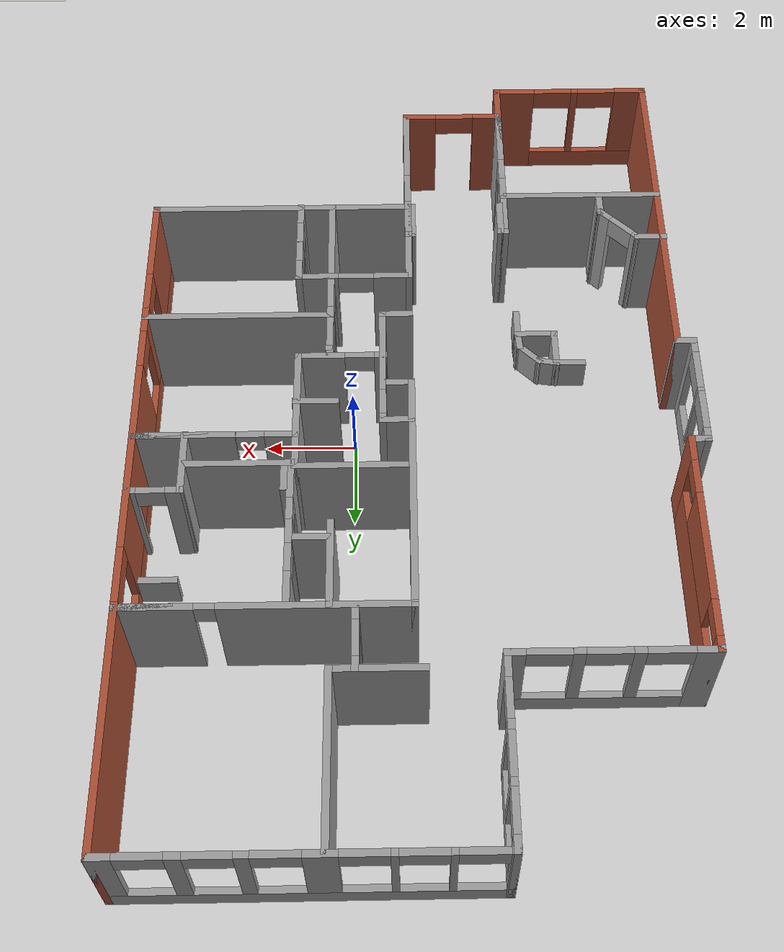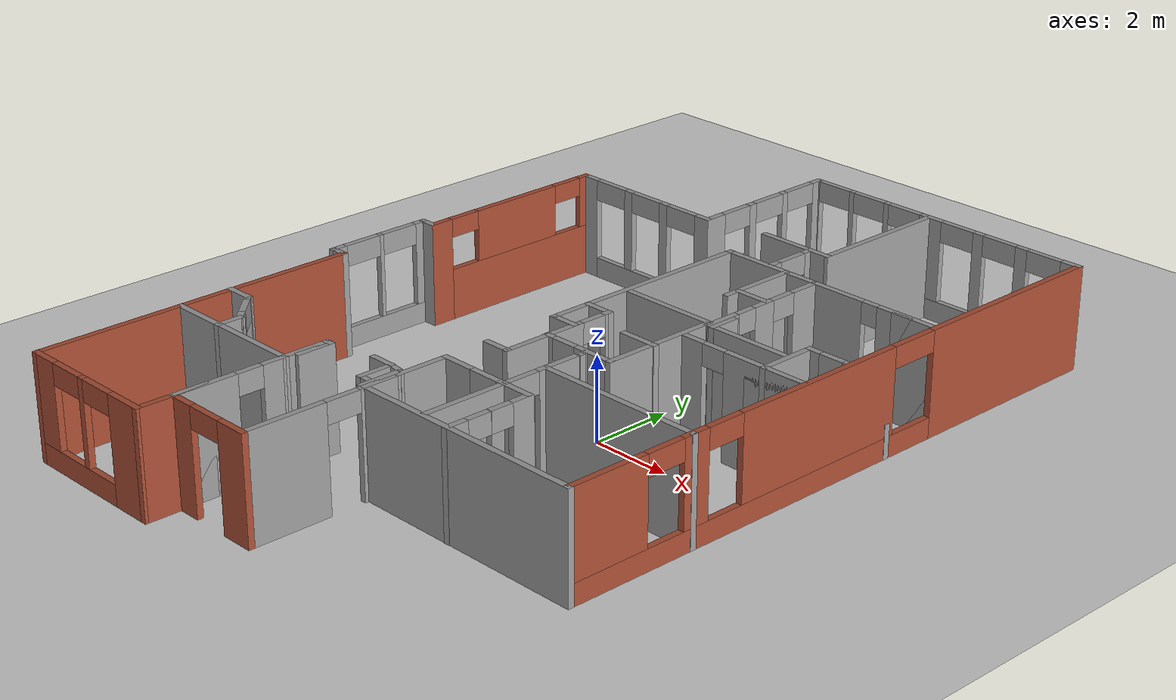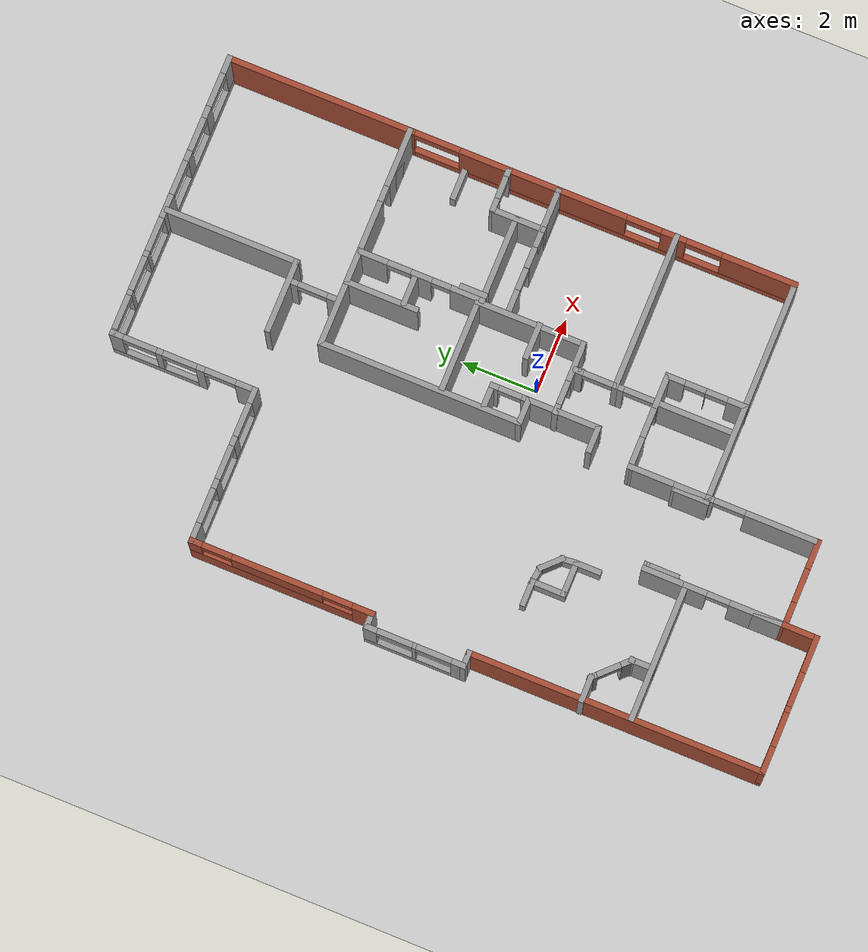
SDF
<sdf version="1.6">
 <world name="default">
  <light name="sun" type="directional">
   <pose>0 0 10 0 -0 0</pose>
   <diffuse>0.8 0.8 0.8 1</diffuse>
   <specular>0.2 0.2 0.2 1</specular>
   <attenuation>
    <range>1000</range>
    <constant>0.9</constant>
    <linear>0.01</linear>
    <quadratic>0.001</quadratic>
   </attenuation>
   <direction>-0.5 0.1 -0.9</direction>
  </light>
  <model name="ground_plane">
   <static>1</static>
   <link name="link">
    <collision name="collision">
     <geometry><plane><normal>0 0 1</normal><size>100 100</size></plane></geometry>
     <surface><friction><ode><mu>100</mu><mu2>50</mu2></ode></friction></surface>
    </collision>
    <visual name="visual">
     <cast_shadows>0</cast_shadows>
     <geometry><plane><normal>0 0 1</normal><size>100 100</size></plane></geometry>
     <material>
      <script><uri>file://media/materials/scripts/gazebo.material</uri><name>Gazebo/Grey</name></script>
     </material>
    </visual>
   </link>
  </model>
  <gravity>0 0 -9.8</gravity>
  <magnetic_field>6e-06 2.3e-05 -4.2e-05</magnetic_field>
  <atmosphere type="adiabatic"/>
  <physics name="default_physics" default="0" type="ode">
   <max_step_size>0.001</max_step_size>
   <real_time_factor>1</real_time_factor>
   <real_time_update_rate>1000</real_time_update_rate>
  </physics>
  <scene><ambient>0.4 0.4 0.4 1</ambient><background>0.7 0.7 0.7 1</background><shadows>1</shadows></scene>
  <spherical_coordinates>
   <surface_model>EARTH_WGS84</surface_model>
   <latitude_deg>0</latitude_deg>
   <longitude_deg>0</longitude_deg>
   <elevation>0</elevation>
   <heading_deg>0</heading_deg>
  </spherical_coordinates>
  <model name="Winter_Wren">
   <pose>-1.42891 0.6718 0 0 -0 0</pose>
   <link name="Wall_100">
    <pose>5.45291 1.9622 0 0 -0 0.007619</pose>
    <visual name="Wall_100_Visual_0">
     <pose>-0.407439 0 1.25 0 -0 0</pose>
     <geometry><box><size>0.385122 0.15 2.5</size></box></geometry>
     <material>
      <script><uri>file://media/materials/scripts/gazebo.material</uri><name>Gazebo/Grey</name></script>
      <ambient>1 1 1 1</ambient>
     </material>
     <meta><layer>0</layer></meta>
    </visual>
    <collision name="Wall_100_Collision_0">
     <geometry><box><size>0.385122 0.15 2.5</size></box></geometry>
     <pose>-0.407439 0 1.25 0 -0 0</pose>
    </collision>
    <visual name="Wall_100_Visual_1">
     <pose>0.493412 0 1.25 0 -0 0</pose>
     <geometry><box><size>0.213175 0.15 2.5</size></box></geometry>
     <material>
      <script><uri>file://media/materials/scripts/gazebo.material</uri><name>Gazebo/Grey</name></script>
      <ambient>1 1 1 1</ambient>
     </material>
     <meta><layer>0</layer></meta>
    </visual>
    <collision name="Wall_100_Collision_1">
     <geometry><box><size>0.213175 0.15 2.5</size></box></geometry>
     <pose>0.493412 0 1.25 0 -0 0</pose>
    </collision>
    <visual name="Wall_100_Visual_2">
     <pose>0.085973 0 2.25 0 -0 0</pose>
     <geometry><box><size>0.601703 0.15 0.5</size></box></geometry>
     <material>
      <script><uri>file://media/materials/scripts/gazebo.material</uri><name>Gazebo/Grey</name></script>
      <ambient>1 1 1 1</ambient>
     </material>
     <meta><layer>0</layer></meta>
    </visual>
    <collision name="Wall_100_Collision_2">
     <geometry><box><size>0.601703 0.15 0.5</size></box></geometry>
     <pose>0.085973 0 2.25 0 -0 0</pose>
    </collision>
   </link>
   <link name="Wall_102">
    <pose>2.68057 2.97391 0 0 -0 1.5712</pose>
    <visual name="Wall_102_Visual_0">
     <pose>-1.25598 0 1.25 0 -0 0</pose>
     <geometry><box><size>0.922652 0.15 2.5</size></box></geometry>
     <material>
      <script><uri>file://media/materials/scripts/gazebo.material</uri><name>Gazebo/Grey</name></script>
      <ambient>1 1 1 1</ambient>
     </material>
     <meta><layer>0</layer></meta>
    </visual>
    <collision name="Wall_102_Collision_0">
     <geometry><box><size>0.922652 0.15 2.5</size></box></geometry>
     <pose>-1.25598 0 1.25 0 -0 0</pose>
    </collision>
    <visual name="Wall_102_Visual_1">
     <pose>-0.005242 0 1.25 0 -0 0</pose>
     <geometry><box><size>0.565593 0.15 2.5</size></box></geometry>
     <material>
      <script><uri>file://media/materials/scripts/gazebo.material</uri><name>Gazebo/Grey</name></script>
      <ambient>1 1 1 1</ambient>
     </material>
     <meta><layer>0</layer></meta>
    </visual>
    <collision name="Wall_102_Collision_1">
     <geometry><box><size>0.565593 0.15 2.5</size></box></geometry>
     <pose>-0.005242 0 1.25 0 -0 0</pose>
    </collision>
    <visual name="Wall_102_Visual_2">
     <pose>1.31557 0 1.25 0 -0 0</pose>
     <geometry><box><size>0.80346 0.15 2.5</size></box></geometry>
     <material>
      <script><uri>file://media/materials/scripts/gazebo.material</uri><name>Gazebo/Grey</name></script>
      <ambient>1 1 1 1</ambient>
     </material>
     <meta><layer>0</layer></meta>
    </visual>
    <collision name="Wall_102_Collision_2">
     <geometry><box><size>0.80346 0.15 2.5</size></box></geometry>
     <pose>1.31557 0 1.25 0 -0 0</pose>
    </collision>
    <visual name="Wall_102_Visual_3">
     <pose>-0.541345 0 2.25 0 -0 0</pose>
     <geometry><box><size>0.506613 0.15 0.5</size></box></geometry>
     <material>
      <script><uri>file://media/materials/scripts/gazebo.material</uri><name>Gazebo/Grey</name></script>
      <ambient>1 1 1 1</ambient>
     </material>
     <meta><layer>0</layer></meta>
    </visual>
    <collision name="Wall_102_Collision_3">
     <geometry><box><size>0.506613 0.15 0.5</size></box></geometry>
     <pose>-0.541345 0 2.25 0 -0 0</pose>
    </collision>
    <visual name="Wall_102_Visual_4">
     <pose>0.595699 0 2.25 0 -0 0</pose>
     <geometry><box><size>0.636289 0.15 0.5</size></box></geometry>
     <material>
      <script><uri>file://media/materials/scripts/gazebo.material</uri><name>Gazebo/Grey</name></script>
      <ambient>1 1 1 1</ambient>
     </material>
     <meta><layer>0</layer></meta>
    </visual>
    <collision name="Wall_102_Collision_4">
     <geometry><box><size>0.636289 0.15 0.5</size></box></geometry>
     <pose>0.595699 0 2.25 0 -0 0</pose>
    </collision>
   </link>
   <link name="Wall_104">
    <collision name="Wall_104_Collision">
     <geometry><box><size>0.95 0.15 2.5</size></box></geometry>
     <pose>0 0 1.25 0 -0 0</pose>
    </collision>
    <visual name="Wall_104_Visual">
     <pose>0 0 1.25 0 -0 0</pose>
     <geometry><box><size>0.95 0.15 2.5</size></box></geometry>
     <material>
      <script><uri>file://media/materials/scripts/gazebo.material</uri><name>Gazebo/Grey</name></script>
      <ambient>1 1 1 1</ambient>
     </material>
     <meta><layer>0</layer></meta>
    </visual>
    <pose>2.27097 3.1122 0 0 -0 3.14159</pose>
   </link>
   <link name="Wall_106">
    <collision name="Wall_106_Collision">
     <geometry><box><size>2 0.15 2.5</size></box></geometry>
     <pose>0 0 1.25 0 -0 0</pose>
    </collision>
    <visual name="Wall_106_Visual">
     <pose>0 0 1.25 0 -0 0</pose>
     <geometry><box><size>2 0.15 2.5</size></box></geometry>
     <material>
      <script><uri>file://media/materials/scripts/gazebo.material</uri><name>Gazebo/Grey</name></script>
      <ambient>1 1 1 1</ambient>
     </material>
     <meta><layer>0</layer></meta>
    </visual>
    <pose>1.83763 3.70673 0 0 -0 1.5708</pose>
   </link>
   <link name="Wall_109">
    <collision name="Wall_109_Collision">
     <geometry><box><size>0.75 0.15 2.5</size></box></geometry>
     <pose>0 0 1.25 0 -0 0</pose>
    </collision>
    <visual name="Wall_109_Visual">
     <pose>0 0 1.25 0 -0 0</pose>
     <geometry><box><size>0.75 0.15 2.5</size></box></geometry>
     <material>
      <script><uri>file://media/materials/scripts/gazebo.material</uri><name>Gazebo/Grey</name></script>
      <ambient>1 1 1 1</ambient>
     </material>
     <meta><layer>0</layer></meta>
    </visual>
    <pose>2.81628 1.62211 0 0 0 -1.5708</pose>
   </link>
   <link name="Wall_11">
    <pose>-6.02991 -0.424563 0 0 -0 1.5708</pose>
    <visual name="Wall_11_Visual_0">
     <pose>-1.17844 0 1.25 0 -0 0</pose>
     <geometry><box><size>0.393121 0.15 2.5</size></box></geometry>
     <material>
      <script><uri>file://media/materials/scripts/gazebo.material</uri><name>Gazebo/Grey</name></script>
      <ambient>1 1 1 1</ambient>
     </material>
     <meta><layer>0</layer></meta>
    </visual>
    <collision name="Wall_11_Collision_0">
     <geometry><box><size>0.393121 0.15 2.5</size></box></geometry>
     <pose>-1.17844 0 1.25 0 -0 0</pose>
    </collision>
    <visual name="Wall_11_Visual_1">
     <pose>0.19656 0 0.25 0 -0 0</pose>
     <geometry><box><size>2.35688 0.15 0.5</size></box></geometry>
     <material>
      <script><uri>file://media/materials/scripts/gazebo.material</uri><name>Gazebo/Grey</name></script>
      <ambient>1 1 1 1</ambient>
     </material>
     <meta><layer>0</layer></meta>
    </visual>
    <collision name="Wall_11_Collision_1">
     <geometry><box><size>2.35688 0.15 0.5</size></box></geometry>
     <pose>0.19656 0 0.25 0 -0 0</pose>
    </collision>
    <visual name="Wall_11_Visual_2">
     <pose>0.019006 0 1.5 0 -0 0</pose>
     <geometry><box><size>0.101771 0.15 2</size></box></geometry>
     <material>
      <script><uri>file://media/materials/scripts/gazebo.material</uri><name>Gazebo/Grey</name></script>
      <ambient>1 1 1 1</ambient>
     </material>
     <meta><layer>0</layer></meta>
    </visual>
    <collision name="Wall_11_Collision_2">
     <geometry><box><size>0.101771 0.15 2</size></box></geometry>
     <pose>0.019006 0 1.5 0 -0 0</pose>
    </collision>
    <visual name="Wall_11_Visual_3">
     <pose>1.19745 0 1.5 0 -0 0</pose>
     <geometry><box><size>0.355108 0.15 2</size></box></geometry>
     <material>
      <script><uri>file://media/materials/scripts/gazebo.material</uri><name>Gazebo/Grey</name></script>
      <ambient>1 1 1 1</ambient>
     </material>
     <meta><layer>0</layer></meta>
    </visual>
    <collision name="Wall_11_Collision_3">
     <geometry><box><size>0.355108 0.15 2</size></box></geometry>
     <pose>1.19745 0 1.5 0 -0 0</pose>
    </collision>
    <visual name="Wall_11_Visual_4">
     <pose>-0.506879 0 2.25 0 -0 0</pose>
     <geometry><box><size>0.95 0.15 0.5</size></box></geometry>
     <material>
      <script><uri>file://media/materials/scripts/gazebo.material</uri><name>Gazebo/Grey</name></script>
      <ambient>1 1 1 1</ambient>
     </material>
     <meta><layer>0</layer></meta>
    </visual>
    <collision name="Wall_11_Collision_4">
     <geometry><box><size>0.95 0.15 0.5</size></box></geometry>
     <pose>-0.506879 0 2.25 0 -0 0</pose>
    </collision>
    <visual name="Wall_11_Visual_5">
     <pose>0.544892 0 2.25 0 -0 0</pose>
     <geometry><box><size>0.95 0.15 0.5</size></box></geometry>
     <material>
      <script><uri>file://media/materials/scripts/gazebo.material</uri><name>Gazebo/Grey</name></script>
      <ambient>1 1 1 1</ambient>
     </material>
     <meta><layer>0</layer></meta>
    </visual>
    <collision name="Wall_11_Collision_5">
     <geometry><box><size>0.95 0.15 0.5</size></box></geometry>
     <pose>0.544892 0 2.25 0 -0 0</pose>
    </collision>
   </link>
   <link name="Wall_111">
    <collision name="Wall_111_Collision">
     <geometry><box><size>1 0.15 0.813</size></box></geometry>
     <pose>0 0 0.4065 0 -0 0</pose>
    </collision>
    <visual name="Wall_111_Visual">
     <pose>0 0 0.4065 0 -0 0</pose>
     <geometry><box><size>1 0.15 0.813</size></box></geometry>
     <material>
      <script><uri>file://media/materials/scripts/gazebo.material</uri><name>Gazebo/Grey</name></script>
      <ambient>1 1 1 1</ambient>
     </material>
     <meta><layer>0</layer></meta>
    </visual>
    <pose>5.60491 3.1252 0 0 -0 3.14159</pose>
   </link>
   <link name="Wall_113">
    <collision name="Wall_113_Collision">
     <geometry><box><size>1 0.15 2.5</size></box></geometry>
     <pose>0 0 1.25 0 -0 0</pose>
    </collision>
    <visual name="Wall_113_Visual">
     <pose>0 0 1.25 0 -0 0</pose>
     <geometry><box><size>1 0.15 2.5</size></box></geometry>
     <material>
      <script><uri>file://media/materials/scripts/gazebo.material</uri><name>Gazebo/Grey</name></script>
      <ambient>1 1 1 1</ambient>
     </material>
     <meta><layer>0</layer></meta>
    </visual>
    <pose>2.20363 -0.230073 0 0 -0 3.14159</pose>
   </link>
   <link name="Wall_115">
    <collision name="Wall_115_Collision">
     <geometry><box><size>2 0.15 2.5</size></box></geometry>
     <pose>0 0 1.25 0 -0 0</pose>
    </collision>
    <visual name="Wall_115_Visual">
     <pose>0 0 1.25 0 -0 0</pose>
     <geometry><box><size>2 0.15 2.5</size></box></geometry>
     <material>
      <script><uri>file://media/materials/scripts/gazebo.material</uri><name>Gazebo/Grey</name></script>
      <ambient>1 1 1 1</ambient>
     </material>
     <meta><layer>0</layer></meta>
    </visual>
    <pose>0.902865 6.01206 0 0 -0 0.000156</pose>
   </link>
   <link name="Wall_117">
    <collision name="Wall_117_Collision">
     <geometry><box><size>3.65 0.15 2.5</size></box></geometry>
     <pose>0 0 1.25 0 -0 0</pose>
    </collision>
    <visual name="Wall_117_Visual">
     <pose>0 0 1.25 0 -0 0</pose>
     <geometry><box><size>3.65 0.15 2.5</size></box></geometry>
     <material>
      <script><uri>file://media/materials/scripts/gazebo.material</uri><name>Gazebo/Grey</name></script>
      <ambient>1 1 1 1</ambient>
     </material>
     <meta><layer>0</layer></meta>
    </visual>
    <pose>1.82791 7.7622 0 0 -0 1.5708</pose>
   </link>
   <link name="Wall_119">
    <pose>1.32474 5.33276 0 0 0 -1.5708</pose>
    <visual name="Wall_119_Visual_0">
     <pose>-0.585981 0 1.25 0 -0 0</pose>
     <geometry><box><size>0.328039 0.15 2.5</size></box></geometry>
     <material>
      <script><uri>file://media/materials/scripts/gazebo.material</uri><name>Gazebo/Grey</name></script>
      <ambient>1 1 1 1</ambient>
     </material>
     <meta><layer>0</layer></meta>
    </visual>
    <collision name="Wall_119_Collision_0">
     <geometry><box><size>0.328039 0.15 2.5</size></box></geometry>
     <pose>-0.585981 0 1.25 0 -0 0</pose>
    </collision>
    <visual name="Wall_119_Visual_1">
     <pose>0.557309 0 1.25 0 -0 0</pose>
     <geometry><box><size>0.385383 0.15 2.5</size></box></geometry>
     <material>
      <script><uri>file://media/materials/scripts/gazebo.material</uri><name>Gazebo/Grey</name></script>
      <ambient>1 1 1 1</ambient>
     </material>
     <meta><layer>0</layer></meta>
    </visual>
    <collision name="Wall_119_Collision_1">
     <geometry><box><size>0.385383 0.15 2.5</size></box></geometry>
     <pose>0.557309 0 1.25 0 -0 0</pose>
    </collision>
    <visual name="Wall_119_Visual_2">
     <pose>-0.028672 0 2.25 0 -0 0</pose>
     <geometry><box><size>0.786578 0.15 0.5</size></box></geometry>
     <material>
      <script><uri>file://media/materials/scripts/gazebo.material</uri><name>Gazebo/Grey</name></script>
      <ambient>1 1 1 1</ambient>
     </material>
     <meta><layer>0</layer></meta>
    </visual>
    <collision name="Wall_119_Collision_2">
     <geometry><box><size>0.786578 0.15 0.5</size></box></geometry>
     <pose>-0.028672 0 2.25 0 -0 0</pose>
    </collision>
   </link>
   <link name="Wall_121">
    <collision name="Wall_121_Collision">
     <geometry><box><size>1.5 0.15 2.5</size></box></geometry>
     <pose>0 0 1.25 0 -0 0</pose>
    </collision>
    <visual name="Wall_121_Visual">
     <pose>0 0 1.25 0 -0 0</pose>
     <geometry><box><size>1.5 0.15 2.5</size></box></geometry>
     <material>
      <script><uri>file://media/materials/scripts/gazebo.material</uri><name>Gazebo/Grey</name></script>
      <ambient>1 1 1 1</ambient>
     </material>
     <meta><layer>0</layer></meta>
    </visual>
    <pose>4.92801 1.28308 0 0 0 -1.57065</pose>
   </link>
   <link name="Wall_13">
    <collision name="Wall_13_Collision">
     <geometry><box><size>0.5 0.15 2.5</size></box></geometry>
     <pose>0 0 1.25 0 -0 0</pose>
    </collision>
    <visual name="Wall_13_Visual">
     <pose>0 0 1.25 0 -0 0</pose>
     <geometry><box><size>0.5 0.15 2.5</size></box></geometry>
     <material>
      <script><uri>file://media/materials/scripts/gazebo.material</uri><name>Gazebo/Grey</name></script>
      <ambient>1 1 1 1</ambient>
     </material>
     <meta><layer>0</layer></meta>
    </visual>
    <pose>-5.85491 0.875437 0 0 -0 0</pose>
   </link>
   <link name="Wall_15">
    <pose>-5.67991 3.30044 0 0 -0 1.5708</pose>
    <visual name="Wall_15_Visual_0">
     <pose>-2.20148 0 1.25 0 -0 0</pose>
     <geometry><box><size>0.59704 0.15 2.5</size></box></geometry>
     <material>
      <script><uri>file://media/materials/scripts/gazebo.material</uri><name>Gazebo/Bricks</name></script>
      <ambient>1 1 1 1</ambient>
     </material>
     <meta><layer>0</layer></meta>
    </visual>
    <collision name="Wall_15_Collision_0">
     <geometry><box><size>0.59704 0.15 2.5</size></box></geometry>
     <pose>-2.20148 0 1.25 0 -0 0</pose>
    </collision>
    <visual name="Wall_15_Visual_1">
     <pose>0.29852 0 0.625 0 -0 0</pose>
     <geometry><box><size>4.40296 0.15 1.25</size></box></geometry>
     <material>
      <script><uri>file://media/materials/scripts/gazebo.material</uri><name>Gazebo/Bricks</name></script>
      <ambient>1 1 1 1</ambient>
     </material>
     <meta><layer>0</layer></meta>
    </visual>
    <collision name="Wall_15_Collision_1">
     <geometry><box><size>4.40296 0.15 1.25</size></box></geometry>
     <pose>0.29852 0 0.625 0 -0 0</pose>
    </collision>
    <visual name="Wall_15_Visual_2">
     <pose>0.120492 0 1.875 0 -0 0</pose>
     <geometry><box><size>2.4469 0.15 1.25</size></box></geometry>
     <material>
      <script><uri>file://media/materials/scripts/gazebo.material</uri><name>Gazebo/Bricks</name></script>
      <ambient>1 1 1 1</ambient>
     </material>
     <meta><layer>0</layer></meta>
    </visual>
    <collision name="Wall_15_Collision_2">
     <geometry><box><size>2.4469 0.15 1.25</size></box></geometry>
     <pose>0.120492 0 1.875 0 -0 0</pose>
    </collision>
    <visual name="Wall_15_Visual_3">
     <pose>2.32197 0 1.875 0 -0 0</pose>
     <geometry><box><size>0.356057 0.15 1.25</size></box></geometry>
     <material>
      <script><uri>file://media/materials/scripts/gazebo.material</uri><name>Gazebo/Bricks</name></script>
      <ambient>1 1 1 1</ambient>
     </material>
     <meta><layer>0</layer></meta>
    </visual>
    <collision name="Wall_15_Collision_3">
     <geometry><box><size>0.356057 0.15 1.25</size></box></geometry>
     <pose>2.32197 0 1.875 0 -0 0</pose>
    </collision>
    <visual name="Wall_15_Visual_4">
     <pose>-1.50296 0 2.275 0 -0 0</pose>
     <geometry><box><size>0.8 0.15 0.45</size></box></geometry>
     <material>
      <script><uri>file://media/materials/scripts/gazebo.material</uri><name>Gazebo/Bricks</name></script>
      <ambient>1 1 1 1</ambient>
     </material>
     <meta><layer>0</layer></meta>
    </visual>
    <collision name="Wall_15_Collision_4">
     <geometry><box><size>0.8 0.15 0.45</size></box></geometry>
     <pose>-1.50296 0 2.275 0 -0 0</pose>
    </collision>
    <visual name="Wall_15_Visual_5">
     <pose>1.74394 0 2.275 0 -0 0</pose>
     <geometry><box><size>0.8 0.15 0.45</size></box></geometry>
     <material>
      <script><uri>file://media/materials/scripts/gazebo.material</uri><name>Gazebo/Bricks</name></script>
      <ambient>1 1 1 1</ambient>
     </material>
     <meta><layer>0</layer></meta>
    </visual>
    <collision name="Wall_15_Collision_5">
     <geometry><box><size>0.8 0.15 0.45</size></box></geometry>
     <pose>1.74394 0 2.275 0 -0 0</pose>
    </collision>
   </link>
   <link name="Wall_17">
    <pose>-3.62991 5.72544 0 0 -0 0</pose>
    <visual name="Wall_17_Visual_0">
     <pose>-1.84959 0 1.25 0 -0 0</pose>
     <geometry><box><size>0.55082 0.15 2.5</size></box></geometry>
     <material>
      <script><uri>file://media/materials/scripts/gazebo.material</uri><name>Gazebo/Grey</name></script>
      <ambient>1 1 1 1</ambient>
     </material>
     <meta><layer>0</layer></meta>
    </visual>
    <collision name="Wall_17_Collision_0">
     <geometry><box><size>0.55082 0.15 2.5</size></box></geometry>
     <pose>-1.84959 0 1.25 0 -0 0</pose>
    </collision>
    <visual name="Wall_17_Visual_1">
     <pose>0.27541 0 0.25 0 -0 0</pose>
     <geometry><box><size>3.69918 0.15 0.5</size></box></geometry>
     <material>
      <script><uri>file://media/materials/scripts/gazebo.material</uri><name>Gazebo/Grey</name></script>
      <ambient>1 1 1 1</ambient>
     </material>
     <meta><layer>0</layer></meta>
    </visual>
    <collision name="Wall_17_Collision_1">
     <geometry><box><size>3.69918 0.15 0.5</size></box></geometry>
     <pose>0.27541 0 0.25 0 -0 0</pose>
    </collision>
    <visual name="Wall_17_Visual_2">
     <pose>-0.504959 0 1.5 0 -0 0</pose>
     <geometry><box><size>0.252442 0.15 2</size></box></geometry>
     <material>
      <script><uri>file://media/materials/scripts/gazebo.material</uri><name>Gazebo/Grey</name></script>
      <ambient>1 1 1 1</ambient>
     </material>
     <meta><layer>0</layer></meta>
    </visual>
    <collision name="Wall_17_Collision_2">
     <geometry><box><size>0.252442 0.15 2</size></box></geometry>
     <pose>-0.504959 0 1.5 0 -0 0</pose>
    </collision>
    <visual name="Wall_17_Visual_3">
     <pose>0.660585 0 1.5 0 -0 0</pose>
     <geometry><box><size>0.252646 0.15 2</size></box></geometry>
     <material>
      <script><uri>file://media/materials/scripts/gazebo.material</uri><name>Gazebo/Grey</name></script>
      <ambient>1 1 1 1</ambient>
     </material>
     <meta><layer>0</layer></meta>
    </visual>
    <collision name="Wall_17_Collision_3">
     <geometry><box><size>0.252646 0.15 2</size></box></geometry>
     <pose>0.660585 0 1.5 0 -0 0</pose>
    </collision>
    <visual name="Wall_17_Visual_4">
     <pose>1.90845 0 1.5 0 -0 0</pose>
     <geometry><box><size>0.433092 0.15 2</size></box></geometry>
     <material>
      <script><uri>file://media/materials/scripts/gazebo.material</uri><name>Gazebo/Grey</name></script>
      <ambient>1 1 1 1</ambient>
     </material>
     <meta><layer>0</layer></meta>
    </visual>
    <collision name="Wall_17_Collision_4">
     <geometry><box><size>0.433092 0.15 2</size></box></geometry>
     <pose>1.90845 0 1.5 0 -0 0</pose>
    </collision>
    <visual name="Wall_17_Visual_5">
     <pose>-1.10268 0 2.25 0 -0 0</pose>
     <geometry><box><size>0.943 0.15 0.5</size></box></geometry>
     <material>
      <script><uri>file://media/materials/scripts/gazebo.material</uri><name>Gazebo/Grey</name></script>
      <ambient>1 1 1 1</ambient>
     </material>
     <meta><layer>0</layer></meta>
    </visual>
    <collision name="Wall_17_Collision_5">
     <geometry><box><size>0.943 0.15 0.5</size></box></geometry>
     <pose>-1.10268 0 2.25 0 -0 0</pose>
    </collision>
    <visual name="Wall_17_Visual_6">
     <pose>0.077763 0 2.25 0 -0 0</pose>
     <geometry><box><size>0.913 0.15 0.5</size></box></geometry>
     <material>
      <script><uri>file://media/materials/scripts/gazebo.material</uri><name>Gazebo/Grey</name></script>
      <ambient>1 1 1 1</ambient>
     </material>
     <meta><layer>0</layer></meta>
    </visual>
    <collision name="Wall_17_Collision_6">
     <geometry><box><size>0.913 0.15 0.5</size></box></geometry>
     <pose>0.077763 0 2.25 0 -0 0</pose>
    </collision>
    <visual name="Wall_17_Visual_7">
     <pose>1.23941 0 2.25 0 -0 0</pose>
     <geometry><box><size>0.905 0.15 0.5</size></box></geometry>
     <material>
      <script><uri>file://media/materials/scripts/gazebo.material</uri><name>Gazebo/Grey</name></script>
      <ambient>1 1 1 1</ambient>
     </material>
     <meta><layer>0</layer></meta>
    </visual>
    <collision name="Wall_17_Collision_7">
     <geometry><box><size>0.905 0.15 0.5</size></box></geometry>
     <pose>1.23941 0 2.25 0 -0 0</pose>
    </collision>
   </link>
   <link name="Wall_19">
    <pose>-1.57991 7.65044 0 0 -0 1.5708</pose>
    <visual name="Wall_19_Visual_0">
     <pose>-1.70598 0 1.25 0 -0 0</pose>
     <geometry><box><size>0.588032 0.15 2.5</size></box></geometry>
     <material>
      <script><uri>file://media/materials/scripts/gazebo.material</uri><name>Gazebo/Grey</name></script>
      <ambient>1 1 1 1</ambient>
     </material>
     <meta><layer>0</layer></meta>
    </visual>
    <collision name="Wall_19_Collision_0">
     <geometry><box><size>0.588032 0.15 2.5</size></box></geometry>
     <pose>-1.70598 0 1.25 0 -0 0</pose>
    </collision>
    <visual name="Wall_19_Visual_1">
     <pose>-0.462155 0 1.25 0 -0 0</pose>
     <geometry><box><size>0.220609 0.15 2.5</size></box></geometry>
     <material>
      <script><uri>file://media/materials/scripts/gazebo.material</uri><name>Gazebo/Grey</name></script>
      <ambient>1 1 1 1</ambient>
     </material>
     <meta><layer>0</layer></meta>
    </visual>
    <collision name="Wall_19_Collision_1">
     <geometry><box><size>0.220609 0.15 2.5</size></box></geometry>
     <pose>-0.462155 0 1.25 0 -0 0</pose>
    </collision>
    <visual name="Wall_19_Visual_2">
     <pose>0.824075 0 0.25 0 -0 0</pose>
     <geometry><box><size>2.35185 0.15 0.5</size></box></geometry>
     <material>
      <script><uri>file://media/materials/scripts/gazebo.material</uri><name>Gazebo/Grey</name></script>
      <ambient>1 1 1 1</ambient>
     </material>
     <meta><layer>0</layer></meta>
    </visual>
    <collision name="Wall_19_Collision_2">
     <geometry><box><size>2.35185 0.15 0.5</size></box></geometry>
     <pose>0.824075 0 0.25 0 -0 0</pose>
    </collision>
    <visual name="Wall_19_Visual_3">
     <pose>0.653344 0 1.5 0 -0 0</pose>
     <geometry><box><size>0.16979 0.15 2</size></box></geometry>
     <material>
      <script><uri>file://media/materials/scripts/gazebo.material</uri><name>Gazebo/Grey</name></script>
      <ambient>1 1 1 1</ambient>
     </material>
     <meta><layer>0</layer></meta>
    </visual>
    <collision name="Wall_19_Collision_3">
     <geometry><box><size>0.16979 0.15 2</size></box></geometry>
     <pose>0.653344 0 1.5 0 -0 0</pose>
    </collision>
    <visual name="Wall_19_Visual_4">
     <pose>1.81812 0 1.5 0 -0 0</pose>
     <geometry><box><size>0.363761 0.15 2</size></box></geometry>
     <material>
      <script><uri>file://media/materials/scripts/gazebo.material</uri><name>Gazebo/Grey</name></script>
      <ambient>1 1 1 1</ambient>
     </material>
     <meta><layer>0</layer></meta>
    </visual>
    <collision name="Wall_19_Collision_4">
     <geometry><box><size>0.363761 0.15 2</size></box></geometry>
     <pose>1.81812 0 1.5 0 -0 0</pose>
    </collision>
    <visual name="Wall_19_Visual_5">
     <pose>-0.992214 0 2.25 0 -0 0</pose>
     <geometry><box><size>0.839509 0.15 0.5</size></box></geometry>
     <material>
      <script><uri>file://media/materials/scripts/gazebo.material</uri><name>Gazebo/Grey</name></script>
      <ambient>1 1 1 1</ambient>
     </material>
     <meta><layer>0</layer></meta>
    </visual>
    <collision name="Wall_19_Collision_5">
     <geometry><box><size>0.839509 0.15 0.5</size></box></geometry>
     <pose>-0.992214 0 2.25 0 -0 0</pose>
    </collision>
    <visual name="Wall_19_Visual_6">
     <pose>0.108299 0 2.25 0 -0 0</pose>
     <geometry><box><size>0.9203 0.15 0.5</size></box></geometry>
     <material>
      <script><uri>file://media/materials/scripts/gazebo.material</uri><name>Gazebo/Grey</name></script>
      <ambient>1 1 1 1</ambient>
     </material>
     <meta><layer>0</layer></meta>
    </visual>
    <collision name="Wall_19_Collision_6">
     <geometry><box><size>0.9203 0.15 0.5</size></box></geometry>
     <pose>0.108299 0 2.25 0 -0 0</pose>
    </collision>
    <visual name="Wall_19_Visual_7">
     <pose>1.18724 0 2.25 0 -0 0</pose>
     <geometry><box><size>0.898 0.15 0.5</size></box></geometry>
     <material>
      <script><uri>file://media/materials/scripts/gazebo.material</uri><name>Gazebo/Grey</name></script>
      <ambient>1 1 1 1</ambient>
     </material>
     <meta><layer>0</layer></meta>
    </visual>
    <collision name="Wall_19_Collision_7">
     <geometry><box><size>0.898 0.15 0.5</size></box></geometry>
     <pose>1.18724 0 2.25 0 -0 0</pose>
    </collision>
   </link>
   <link name="Wall_2">
    <pose>-3.87991 -9.57456 0 0 -0 3.14159</pose>
    <visual name="Wall_2_Visual_0">
     <pose>-1.37369 0 1.25 0 -0 0</pose>
     <geometry><box><size>1.00262 0.15 2.5</size></box></geometry>
     <material>
      <script><uri>file://media/materials/scripts/gazebo.material</uri><name>Gazebo/Bricks</name></script>
      <ambient>1 1 1 1</ambient>
     </material>
     <meta><layer>0</layer></meta>
    </visual>
    <collision name="Wall_2_Collision_0">
     <geometry><box><size>1.00262 0.15 2.5</size></box></geometry>
     <pose>-1.37369 0 1.25 0 -0 0</pose>
    </collision>
    <visual name="Wall_2_Visual_1">
     <pose>0.50131 0 0.25 0 -0 0</pose>
     <geometry><box><size>2.74738 0.15 0.5</size></box></geometry>
     <material>
      <script><uri>file://media/materials/scripts/gazebo.material</uri><name>Gazebo/Bricks</name></script>
      <ambient>1 1 1 1</ambient>
     </material>
     <meta><layer>0</layer></meta>
    </visual>
    <collision name="Wall_2_Collision_1">
     <geometry><box><size>2.74738 0.15 0.5</size></box></geometry>
     <pose>0.50131 0 0.25 0 -0 0</pose>
    </collision>
    <visual name="Wall_2_Visual_2">
     <pose>0.12171 0 1.5 0 -0 0</pose>
     <geometry><box><size>0.16218 0.15 2</size></box></geometry>
     <material>
      <script><uri>file://media/materials/scripts/gazebo.material</uri><name>Gazebo/Bricks</name></script>
      <ambient>1 1 1 1</ambient>
     </material>
     <meta><layer>0</layer></meta>
    </visual>
    <collision name="Wall_2_Collision_2">
     <geometry><box><size>0.16218 0.15 2</size></box></geometry>
     <pose>0.12171 0 1.5 0 -0 0</pose>
    </collision>
    <visual name="Wall_2_Visual_3">
     <pose>1.4954 0 1.5 0 -0 0</pose>
     <geometry><box><size>0.759201 0.15 2</size></box></geometry>
     <material>
      <script><uri>file://media/materials/scripts/gazebo.material</uri><name>Gazebo/Bricks</name></script>
      <ambient>1 1 1 1</ambient>
     </material>
     <meta><layer>0</layer></meta>
    </visual>
    <collision name="Wall_2_Collision_3">
     <geometry><box><size>0.759201 0.15 2</size></box></geometry>
     <pose>1.4954 0 1.5 0 -0 0</pose>
    </collision>
    <visual name="Wall_2_Visual_4">
     <pose>-0.41588 0 2.25 0 -0 0</pose>
     <geometry><box><size>0.913 0.15 0.5</size></box></geometry>
     <material>
      <script><uri>file://media/materials/scripts/gazebo.material</uri><name>Gazebo/Bricks</name></script>
      <ambient>1 1 1 1</ambient>
     </material>
     <meta><layer>0</layer></meta>
    </visual>
    <collision name="Wall_2_Collision_4">
     <geometry><box><size>0.913 0.15 0.5</size></box></geometry>
     <pose>-0.41588 0 2.25 0 -0 0</pose>
    </collision>
    <visual name="Wall_2_Visual_5">
     <pose>0.659299 0 2.25 0 -0 0</pose>
     <geometry><box><size>0.913 0.15 0.5</size></box></geometry>
     <material>
      <script><uri>file://media/materials/scripts/gazebo.material</uri><name>Gazebo/Bricks</name></script>
      <ambient>1 1 1 1</ambient>
     </material>
     <meta><layer>0</layer></meta>
    </visual>
    <collision name="Wall_2_Collision_5">
     <geometry><box><size>0.913 0.15 0.5</size></box></geometry>
     <pose>0.659299 0 2.25 0 -0 0</pose>
    </collision>
   </link>
   <link name="Wall_21">
    <pose>2.22009 9.57544 0 0 -0 0</pose>
    <visual name="Wall_21_Visual_0">
     <pose>-3.78426 0 1.25 0 -0 0</pose>
     <geometry><box><size>0.181482 0.15 2.5</size></box></geometry>
     <material>
      <script><uri>file://media/materials/scripts/gazebo.material</uri><name>Gazebo/Grey</name></script>
      <ambient>1 1 1 1</ambient>
     </material>
     <meta><layer>0</layer></meta>
    </visual>
    <collision name="Wall_21_Collision_0">
     <geometry><box><size>0.181482 0.15 2.5</size></box></geometry>
     <pose>-3.78426 0 1.25 0 -0 0</pose>
    </collision>
    <visual name="Wall_21_Visual_1">
     <pose>0.090741 0 0.25 0 -0 0</pose>
     <geometry><box><size>7.56852 0.15 0.5</size></box></geometry>
     <material>
      <script><uri>file://media/materials/scripts/gazebo.material</uri><name>Gazebo/Grey</name></script>
      <ambient>1 1 1 1</ambient>
     </material>
     <meta><layer>0</layer></meta>
    </visual>
    <collision name="Wall_21_Collision_1">
     <geometry><box><size>7.56852 0.15 0.5</size></box></geometry>
     <pose>0.090741 0 0.25 0 -0 0</pose>
    </collision>
    <visual name="Wall_21_Visual_2">
     <pose>-2.68851 0 1.5 0 -0 0</pose>
     <geometry><box><size>0.140011 0.15 2</size></box></geometry>
     <material>
      <script><uri>file://media/materials/scripts/gazebo.material</uri><name>Gazebo/Grey</name></script>
      <ambient>1 1 1 1</ambient>
     </material>
     <meta><layer>0</layer></meta>
    </visual>
    <collision name="Wall_21_Collision_2">
     <geometry><box><size>0.140011 0.15 2</size></box></geometry>
     <pose>-2.68851 0 1.5 0 -0 0</pose>
    </collision>
    <visual name="Wall_21_Visual_3">
     <pose>-1.62413 0 1.5 0 -0 0</pose>
     <geometry><box><size>0.148154 0.15 2</size></box></geometry>
     <material>
      <script><uri>file://media/materials/scripts/gazebo.material</uri><name>Gazebo/Grey</name></script>
      <ambient>1 1 1 1</ambient>
     </material>
     <meta><layer>0</layer></meta>
    </visual>
    <collision name="Wall_21_Collision_3">
     <geometry><box><size>0.148154 0.15 2</size></box></geometry>
     <pose>-1.62413 0 1.5 0 -0 0</pose>
    </collision>
    <visual name="Wall_21_Visual_4">
     <pose>-0.302512 0 1.5 0 -0 0</pose>
     <geometry><box><size>0.647083 0.15 2</size></box></geometry>
     <material>
      <script><uri>file://media/materials/scripts/gazebo.material</uri><name>Gazebo/Grey</name></script>
      <ambient>1 1 1 1</ambient>
     </material>
     <meta><layer>0</layer></meta>
    </visual>
    <collision name="Wall_21_Collision_4">
     <geometry><box><size>0.647083 0.15 2</size></box></geometry>
     <pose>-0.302512 0 1.5 0 -0 0</pose>
    </collision>
    <visual name="Wall_21_Visual_5">
     <pose>1.08803 0 1.5 0 -0 0</pose>
     <geometry><box><size>0.285999 0.15 2</size></box></geometry>
     <material>
      <script><uri>file://media/materials/scripts/gazebo.material</uri><name>Gazebo/Grey</name></script>
      <ambient>1 1 1 1</ambient>
     </material>
     <meta><layer>0</layer></meta>
    </visual>
    <collision name="Wall_21_Collision_5">
     <geometry><box><size>0.285999 0.15 2</size></box></geometry>
     <pose>1.08803 0 1.5 0 -0 0</pose>
    </collision>
    <visual name="Wall_21_Visual_6">
     <pose>2.30024 0 1.5 0 -0 0</pose>
     <geometry><box><size>0.31842 0.15 2</size></box></geometry>
     <material>
      <script><uri>file://media/materials/scripts/gazebo.material</uri><name>Gazebo/Grey</name></script>
      <ambient>1 1 1 1</ambient>
     </material>
     <meta><layer>0</layer></meta>
    </visual>
    <collision name="Wall_21_Collision_6">
     <geometry><box><size>0.31842 0.15 2</size></box></geometry>
     <pose>2.30024 0 1.5 0 -0 0</pose>
    </collision>
    <visual name="Wall_21_Visual_7">
     <pose>3.62622 0 1.5 0 -0 0</pose>
     <geometry><box><size>0.497552 0.15 2</size></box></geometry>
     <material>
      <script><uri>file://media/materials/scripts/gazebo.material</uri><name>Gazebo/Grey</name></script>
      <ambient>1 1 1 1</ambient>
     </material>
     <meta><layer>0</layer></meta>
    </visual>
    <collision name="Wall_21_Collision_7">
     <geometry><box><size>0.497552 0.15 2</size></box></geometry>
     <pose>3.62622 0 1.5 0 -0 0</pose>
    </collision>
    <visual name="Wall_21_Visual_8">
     <pose>-3.22602 0 2.25 0 -0 0</pose>
     <geometry><box><size>0.935 0.15 0.5</size></box></geometry>
     <material>
      <script><uri>file://media/materials/scripts/gazebo.material</uri><name>Gazebo/Grey</name></script>
      <ambient>1 1 1 1</ambient>
     </material>
     <meta><layer>0</layer></meta>
    </visual>
    <collision name="Wall_21_Collision_8">
     <geometry><box><size>0.935 0.15 0.5</size></box></geometry>
     <pose>-3.22602 0 2.25 0 -0 0</pose>
    </collision>
    <visual name="Wall_21_Visual_9">
     <pose>-2.15836 0 2.25 0 -0 0</pose>
     <geometry><box><size>0.9203 0.15 0.5</size></box></geometry>
     <material>
      <script><uri>file://media/materials/scripts/gazebo.material</uri><name>Gazebo/Grey</name></script>
      <ambient>1 1 1 1</ambient>
     </material>
     <meta><layer>0</layer></meta>
    </visual>
    <collision name="Wall_21_Collision_9">
     <geometry><box><size>0.9203 0.15 0.5</size></box></geometry>
     <pose>-2.15836 0 2.25 0 -0 0</pose>
    </collision>
    <visual name="Wall_21_Visual_10">
     <pose>-1.08805 0 2.25 0 -0 0</pose>
     <geometry><box><size>0.924 0.15 0.5</size></box></geometry>
     <material>
      <script><uri>file://media/materials/scripts/gazebo.material</uri><name>Gazebo/Grey</name></script>
      <ambient>1 1 1 1</ambient>
     </material>
     <meta><layer>0</layer></meta>
    </visual>
    <collision name="Wall_21_Collision_10">
     <geometry><box><size>0.924 0.15 0.5</size></box></geometry>
     <pose>-1.08805 0 2.25 0 -0 0</pose>
    </collision>
    <visual name="Wall_21_Visual_11">
     <pose>0.48303 0 2.25 0 -0 0</pose>
     <geometry><box><size>0.924 0.15 0.5</size></box></geometry>
     <material>
      <script><uri>file://media/materials/scripts/gazebo.material</uri><name>Gazebo/Grey</name></script>
      <ambient>1 1 1 1</ambient>
     </material>
     <meta><layer>0</layer></meta>
    </visual>
    <collision name="Wall_21_Collision_11">
     <geometry><box><size>0.924 0.15 0.5</size></box></geometry>
     <pose>0.48303 0 2.25 0 -0 0</pose>
    </collision>
    <visual name="Wall_21_Visual_12">
     <pose>1.68603 0 2.25 0 -0 0</pose>
     <geometry><box><size>0.91 0.15 0.5</size></box></geometry>
     <material>
      <script><uri>file://media/materials/scripts/gazebo.material</uri><name>Gazebo/Grey</name></script>
      <ambient>1 1 1 1</ambient>
     </material>
     <meta><layer>0</layer></meta>
    </visual>
    <collision name="Wall_21_Collision_12">
     <geometry><box><size>0.91 0.15 0.5</size></box></geometry>
     <pose>1.68603 0 2.25 0 -0 0</pose>
    </collision>
    <visual name="Wall_21_Visual_13">
     <pose>2.91845 0 2.25 0 -0 0</pose>
     <geometry><box><size>0.918 0.15 0.5</size></box></geometry>
     <material>
      <script><uri>file://media/materials/scripts/gazebo.material</uri><name>Gazebo/Grey</name></script>
      <ambient>1 1 1 1</ambient>
     </material>
     <meta><layer>0</layer></meta>
    </visual>
    <collision name="Wall_21_Collision_13">
     <geometry><box><size>0.918 0.15 0.5</size></box></geometry>
     <pose>2.91845 0 2.25 0 -0 0</pose>
    </collision>
   </link>
   <link name="Wall_23">
    <pose>6.02009 1.90044 0 0 0 -1.5708</pose>
    <visual name="Wall_23_Visual_0">
     <pose>-5.18257 0 1.25 0 -0 0</pose>
     <geometry><box><size>5.13486 0.15 2.5</size></box></geometry>
     <material>
      <script><uri>file://media/materials/scripts/gazebo.material</uri><name>Gazebo/Bricks</name></script>
      <ambient>1 1 1 1</ambient>
     </material>
     <meta><layer>0</layer></meta>
    </visual>
    <collision name="Wall_23_Collision_0">
     <geometry><box><size>5.13486 0.15 2.5</size></box></geometry>
     <pose>-5.18257 0 1.25 0 -0 0</pose>
    </collision>
    <visual name="Wall_23_Visual_1">
     <pose>2.56743 0 0.25 0 -0 0</pose>
     <geometry><box><size>10.3651 0.15 0.5</size></box></geometry>
     <material>
      <script><uri>file://media/materials/scripts/gazebo.material</uri><name>Gazebo/Bricks</name></script>
      <ambient>1 1 1 1</ambient>
     </material>
     <meta><layer>0</layer></meta>
    </visual>
    <collision name="Wall_23_Collision_1">
     <geometry><box><size>10.3651 0.15 0.5</size></box></geometry>
     <pose>2.56743 0 0.25 0 -0 0</pose>
    </collision>
    <visual name="Wall_23_Visual_2">
     <pose>0.86981 0 1.5 0 -0 0</pose>
     <geometry><box><size>4.5239 0.15 2</size></box></geometry>
     <material>
      <script><uri>file://media/materials/scripts/gazebo.material</uri><name>Gazebo/Bricks</name></script>
      <ambient>1 1 1 1</ambient>
     </material>
     <meta><layer>0</layer></meta>
    </visual>
    <collision name="Wall_23_Collision_2">
     <geometry><box><size>4.5239 0.15 2</size></box></geometry>
     <pose>0.86981 0 1.5 0 -0 0</pose>
    </collision>
    <visual name="Wall_23_Visual_3">
     <pose>4.40791 0 1.5 0 -0 0</pose>
     <geometry><box><size>0.666289 0.15 2</size></box></geometry>
     <material>
      <script><uri>file://media/materials/scripts/gazebo.material</uri><name>Gazebo/Bricks</name></script>
      <ambient>1 1 1 1</ambient>
     </material>
     <meta><layer>0</layer></meta>
    </visual>
    <collision name="Wall_23_Collision_3">
     <geometry><box><size>0.666289 0.15 2</size></box></geometry>
     <pose>4.40791 0 1.5 0 -0 0</pose>
    </collision>
    <visual name="Wall_23_Visual_4">
     <pose>6.72802 0 1.5 0 -0 0</pose>
     <geometry><box><size>2.04395 0.15 2</size></box></geometry>
     <material>
      <script><uri>file://media/materials/scripts/gazebo.material</uri><name>Gazebo/Bricks</name></script>
      <ambient>1 1 1 1</ambient>
     </material>
     <meta><layer>0</layer></meta>
    </visual>
    <collision name="Wall_23_Collision_4">
     <geometry><box><size>2.04395 0.15 2</size></box></geometry>
     <pose>6.72802 0 1.5 0 -0 0</pose>
    </collision>
    <visual name="Wall_23_Visual_5">
     <pose>-2.00364 0 2.25 0 -0 0</pose>
     <geometry><box><size>1.223 0.15 0.5</size></box></geometry>
     <material>
      <script><uri>file://media/materials/scripts/gazebo.material</uri><name>Gazebo/Bricks</name></script>
      <ambient>1 1 1 1</ambient>
     </material>
     <meta><layer>0</layer></meta>
    </visual>
    <collision name="Wall_23_Collision_5">
     <geometry><box><size>1.223 0.15 0.5</size></box></geometry>
     <pose>-2.00364 0 2.25 0 -0 0</pose>
    </collision>
    <visual name="Wall_23_Visual_6">
     <pose>3.60326 0 2.25 0 -0 0</pose>
     <geometry><box><size>0.943 0.15 0.5</size></box></geometry>
     <material>
      <script><uri>file://media/materials/scripts/gazebo.material</uri><name>Gazebo/Bricks</name></script>
      <ambient>1 1 1 1</ambient>
     </material>
     <meta><layer>0</layer></meta>
    </visual>
    <collision name="Wall_23_Collision_6">
     <geometry><box><size>0.943 0.15 0.5</size></box></geometry>
     <pose>3.60326 0 2.25 0 -0 0</pose>
    </collision>
    <visual name="Wall_23_Visual_7">
     <pose>5.22355 0 2.25 0 -0 0</pose>
     <geometry><box><size>0.965 0.15 0.5</size></box></geometry>
     <material>
      <script><uri>file://media/materials/scripts/gazebo.material</uri><name>Gazebo/Bricks</name></script>
      <ambient>1 1 1 1</ambient>
     </material>
     <meta><layer>0</layer></meta>
    </visual>
    <collision name="Wall_23_Collision_7">
     <geometry><box><size>0.965 0.15 0.5</size></box></geometry>
     <pose>5.22355 0 2.25 0 -0 0</pose>
    </collision>
   </link>
   <link name="Wall_25">
    <collision name="Wall_25_Collision">
     <geometry><box><size>6 0.15 2.5</size></box></geometry>
     <pose>0 0 1.25 0 -0 0</pose>
    </collision>
    <visual name="Wall_25_Visual">
     <pose>0 0 1.25 0 -0 0</pose>
     <geometry><box><size>6 0.15 2.5</size></box></geometry>
     <material>
      <script><uri>file://media/materials/scripts/gazebo.material</uri><name>Gazebo/Grey</name></script>
      <ambient>1 1 1 1</ambient>
     </material>
     <meta><layer>0</layer></meta>
    </visual>
    <pose>3.09509 -5.77456 0 0 -0 3.14159</pose>
   </link>
   <link name="Wall_27">
    <pose>0.170093 -7.19956 0 0 0 -1.5708</pose>
    <visual name="Wall_27_Visual_0">
     <pose>-1.38255 0 1.25 0 -0 0</pose>
     <geometry><box><size>0.23489 0.15 2.5</size></box></geometry>
     <material>
      <script><uri>file://media/materials/scripts/gazebo.material</uri><name>Gazebo/Grey</name></script>
      <ambient>1 1 1 1</ambient>
     </material>
     <meta><layer>0</layer></meta>
    </visual>
    <collision name="Wall_27_Collision_0">
     <geometry><box><size>0.23489 0.15 2.5</size></box></geometry>
     <pose>-1.38255 0 1.25 0 -0 0</pose>
    </collision>
    <visual name="Wall_27_Visual_1">
     <pose>0.537199 0 1.25 0 -0 0</pose>
     <geometry><box><size>1.9256 0.15 2.5</size></box></geometry>
     <material>
      <script><uri>file://media/materials/scripts/gazebo.material</uri><name>Gazebo/Grey</name></script>
      <ambient>1 1 1 1</ambient>
     </material>
     <meta><layer>0</layer></meta>
    </visual>
    <collision name="Wall_27_Collision_1">
     <geometry><box><size>1.9256 0.15 2.5</size></box></geometry>
     <pose>0.537199 0 1.25 0 -0 0</pose>
    </collision>
    <visual name="Wall_27_Visual_2">
     <pose>-0.845356 0 2.25 0 -0 0</pose>
     <geometry><box><size>0.839509 0.15 0.5</size></box></geometry>
     <material>
      <script><uri>file://media/materials/scripts/gazebo.material</uri><name>Gazebo/Grey</name></script>
      <ambient>1 1 1 1</ambient>
     </material>
     <meta><layer>0</layer></meta>
    </visual>
    <collision name="Wall_27_Collision_2">
     <geometry><box><size>0.839509 0.15 0.5</size></box></geometry>
     <pose>-0.845356 0 2.25 0 -0 0</pose>
    </collision>
   </link>
   <link name="Wall_29">
    <collision name="Wall_29_Collision">
     <geometry><box><size>1.00068 0.15 2.5</size></box></geometry>
     <pose>0 0 1.25 0 -0 0</pose>
    </collision>
    <visual name="Wall_29_Visual">
     <pose>0 0 1.25 0 -0 0</pose>
     <geometry><box><size>1.00068 0.15 2.5</size></box></geometry>
     <material>
      <script><uri>file://media/materials/scripts/gazebo.material</uri><name>Gazebo/Bricks</name></script>
      <ambient>1 1 1 1</ambient>
     </material>
     <meta><layer>0</layer></meta>
    </visual>
    <pose>-2.0775 -9.14968 0 0 -0 1.56513</pose>
   </link>
   <link name="Wall_30">
    <pose>-0.950092 -8.7248 0 0 -0 0</pose>
    <visual name="Wall_30_Visual_0">
     <pose>-0.851077 0 1.25 0 -0 0</pose>
     <geometry><box><size>0.697846 0.15 2.5</size></box></geometry>
     <material>
      <script><uri>file://media/materials/scripts/gazebo.material</uri><name>Gazebo/Bricks</name></script>
      <ambient>1 1 1 1</ambient>
     </material>
     <meta><layer>0</layer></meta>
    </visual>
    <collision name="Wall_30_Collision_0">
     <geometry><box><size>0.697846 0.15 2.5</size></box></geometry>
     <pose>-0.851077 0 1.25 0 -0 0</pose>
    </collision>
    <visual name="Wall_30_Visual_1">
     <pose>0.798923 0 1.25 0 -0 0</pose>
     <geometry><box><size>0.802154 0.15 2.5</size></box></geometry>
     <material>
      <script><uri>file://media/materials/scripts/gazebo.material</uri><name>Gazebo/Bricks</name></script>
      <ambient>1 1 1 1</ambient>
     </material>
     <meta><layer>0</layer></meta>
    </visual>
    <collision name="Wall_30_Collision_1">
     <geometry><box><size>0.802154 0.15 2.5</size></box></geometry>
     <pose>0.798923 0 1.25 0 -0 0</pose>
    </collision>
    <visual name="Wall_30_Visual_2">
     <pose>-0.052154 0 2.25 0 -0 0</pose>
     <geometry><box><size>0.9 0.15 0.5</size></box></geometry>
     <material>
      <script><uri>file://media/materials/scripts/gazebo.material</uri><name>Gazebo/Bricks</name></script>
      <ambient>1 1 1 1</ambient>
     </material>
     <meta><layer>0</layer></meta>
    </visual>
    <collision name="Wall_30_Collision_2">
     <geometry><box><size>0.9 0.15 0.5</size></box></geometry>
     <pose>-0.052154 0 2.25 0 -0 0</pose>
    </collision>
   </link>
   <link name="Wall_32">
    <collision name="Wall_32_Collision">
     <geometry><box><size>3.75 0.15 2.5</size></box></geometry>
     <pose>0 0 1.25 0 -0 0</pose>
    </collision>
    <visual name="Wall_32_Visual">
     <pose>0 0 1.25 0 -0 0</pose>
     <geometry><box><size>3.75 0.15 2.5</size></box></geometry>
     <material>
      <script><uri>file://media/materials/scripts/gazebo.material</uri><name>Gazebo/Grey</name></script>
      <ambient>1 1 1 1</ambient>
     </material>
     <meta><layer>0</layer></meta>
    </visual>
    <pose>-3.87271 -6.0748 0 0 -0 0</pose>
   </link>
   <link name="Wall_33">
    <pose>-2.0739 -7.3998 0 0 0 -1.5717</pose>
    <visual name="Wall_33_Visual_0">
     <pose>-1.08046 0 1.25 0 -0 0</pose>
     <geometry><box><size>0.639083 0.15 2.5</size></box></geometry>
     <material>
      <script><uri>file://media/materials/scripts/gazebo.material</uri><name>Gazebo/Grey</name></script>
      <ambient>1 1 1 1</ambient>
     </material>
     <meta><layer>0</layer></meta>
    </visual>
    <collision name="Wall_33_Collision_0">
     <geometry><box><size>0.639083 0.15 2.5</size></box></geometry>
     <pose>-1.08046 0 1.25 0 -0 0</pose>
    </collision>
    <visual name="Wall_33_Visual_1">
     <pose>0.625881 0 1.25 0 -0 0</pose>
     <geometry><box><size>1.54824 0.15 2.5</size></box></geometry>
     <material>
      <script><uri>file://media/materials/scripts/gazebo.material</uri><name>Gazebo/Grey</name></script>
      <ambient>1 1 1 1</ambient>
     </material>
     <meta><layer>0</layer></meta>
    </visual>
    <collision name="Wall_33_Collision_1">
     <geometry><box><size>1.54824 0.15 2.5</size></box></geometry>
     <pose>0.625881 0 1.25 0 -0 0</pose>
    </collision>
    <visual name="Wall_33_Visual_2">
     <pose>0.943444 0 1.25 0 -0 0</pose>
     <geometry><box><size>0.913113 0.15 2.5</size></box></geometry>
     <material>
      <script><uri>file://media/materials/scripts/gazebo.material</uri><name>Gazebo/Grey</name></script>
      <ambient>1 1 1 1</ambient>
     </material>
     <meta><layer>0</layer></meta>
    </visual>
    <collision name="Wall_33_Collision_2">
     <geometry><box><size>0.913113 0.15 2.5</size></box></geometry>
     <pose>0.943444 0 1.25 0 -0 0</pose>
    </collision>
    <visual name="Wall_33_Visual_3">
     <pose>-0.454686 0 2.25 0 -0 0</pose>
     <geometry><box><size>0.612462 0.15 0.5</size></box></geometry>
     <material>
      <script><uri>file://media/materials/scripts/gazebo.material</uri><name>Gazebo/Grey</name></script>
      <ambient>1 1 1 1</ambient>
     </material>
     <meta><layer>0</layer></meta>
    </visual>
    <collision name="Wall_33_Collision_3">
     <geometry><box><size>0.612462 0.15 0.5</size></box></geometry>
     <pose>-0.454686 0 2.25 0 -0 0</pose>
    </collision>
   </link>
   <link name="Wall_37">
    <collision name="Wall_37_Collision">
     <geometry><box><size>0.75 0.15 2.5</size></box></geometry>
     <pose>0 0 1.25 0 -0 0</pose>
    </collision>
    <visual name="Wall_37_Visual">
     <pose>0 0 1.25 0 -0 0</pose>
     <geometry><box><size>0.75 0.15 2.5</size></box></geometry>
     <material>
      <script><uri>file://media/materials/scripts/gazebo.material</uri><name>Gazebo/Grey</name></script>
      <ambient>1 1 1 1</ambient>
     </material>
     <meta><layer>0</layer></meta>
    </visual>
    <pose>-5.40154 -4.75784 0 0 -0 0</pose>
   </link>
   <link name="Wall_38">
    <pose>-4.71263 -5.14675 0 0 0 -0.785398</pose>
    <visual name="Wall_38_Visual_0">
     <pose>-0.510733 0 1.25 0 -0 0</pose>
     <geometry><box><size>0.228534 0.15 2.5</size></box></geometry>
     <material>
      <script><uri>file://media/materials/scripts/gazebo.material</uri><name>Gazebo/Grey</name></script>
      <ambient>1 1 1 1</ambient>
     </material>
     <meta><layer>0</layer></meta>
    </visual>
    <collision name="Wall_38_Collision_0">
     <geometry><box><size>0.228534 0.15 2.5</size></box></geometry>
     <pose>-0.510733 0 1.25 0 -0 0</pose>
    </collision>
    <visual name="Wall_38_Visual_1">
     <pose>0.438619 0 1.25 0 -0 0</pose>
     <geometry><box><size>0.372763 0.15 2.5</size></box></geometry>
     <material>
      <script><uri>file://media/materials/scripts/gazebo.material</uri><name>Gazebo/Grey</name></script>
      <ambient>1 1 1 1</ambient>
     </material>
     <meta><layer>0</layer></meta>
    </visual>
    <collision name="Wall_38_Collision_1">
     <geometry><box><size>0.372763 0.15 2.5</size></box></geometry>
     <pose>0.438619 0 1.25 0 -0 0</pose>
    </collision>
    <visual name="Wall_38_Visual_2">
     <pose>-0.072114 0 2.25 0 -0 0</pose>
     <geometry><box><size>0.648703 0.15 0.5</size></box></geometry>
     <material>
      <script><uri>file://media/materials/scripts/gazebo.material</uri><name>Gazebo/Grey</name></script>
      <ambient>1 1 1 1</ambient>
     </material>
     <meta><layer>0</layer></meta>
    </visual>
    <collision name="Wall_38_Collision_2">
     <geometry><box><size>0.648703 0.15 0.5</size></box></geometry>
     <pose>-0.072114 0 2.25 0 -0 0</pose>
    </collision>
   </link>
   <link name="Wall_39">
    <collision name="Wall_39_Collision">
     <geometry><box><size>0.16 0.15 2.5</size></box></geometry>
     <pose>0 0 1.25 0 -0 0</pose>
    </collision>
    <visual name="Wall_39_Visual">
     <pose>0 0 1.25 0 -0 0</pose>
     <geometry><box><size>0.16 0.15 2.5</size></box></geometry>
     <material>
      <script><uri>file://media/materials/scripts/gazebo.material</uri><name>Gazebo/Grey</name></script>
      <ambient>1 1 1 1</ambient>
     </material>
     <meta><layer>0</layer></meta>
    </visual>
    <pose>-4.31891 -5.53573 0 0 0 -0.014988</pose>
   </link>
   <link name="Wall_4">
    <collision name="Wall_4_Collision">
     <geometry><box><size>8 0.15 2.5</size></box></geometry>
     <pose>0 0 1.25 0 -0 0</pose>
    </collision>
    <visual name="Wall_4_Visual">
     <pose>0 0 1.25 0 -0 0</pose>
     <geometry><box><size>8 0.15 2.5</size></box></geometry>
     <material>
      <script><uri>file://media/materials/scripts/gazebo.material</uri><name>Gazebo/Bricks</name></script>
      <ambient>1 1 1 1</ambient>
     </material>
     <meta><layer>0</layer></meta>
    </visual>
    <pose>-5.67991 -5.64956 0 0 -0 1.5708</pose>
   </link>
   <link name="Wall_40">
    <collision name="Wall_40_Collision">
     <geometry><box><size>0.69 0.15 2.5</size></box></geometry>
     <pose>0 0 1.25 0 -0 0</pose>
    </collision>
    <visual name="Wall_40_Visual">
     <pose>0 0 1.25 0 -0 0</pose>
     <geometry><box><size>0.69 0.15 2.5</size></box></geometry>
     <material>
      <script><uri>file://media/materials/scripts/gazebo.material</uri><name>Gazebo/Grey</name></script>
      <ambient>1 1 1 1</ambient>
     </material>
     <meta><layer>0</layer></meta>
    </visual>
    <pose>-4.31409 -5.8058 0 0 0 -1.5708</pose>
   </link>
   <link name="Wall_42">
    <collision name="Wall_42_Collision">
     <geometry><box><size>1.25 0.15 2.5</size></box></geometry>
     <pose>0 0 1.25 0 -0 0</pose>
    </collision>
    <visual name="Wall_42_Visual">
     <pose>0 0 1.25 0 -0 0</pose>
     <geometry><box><size>1.25 0.15 2.5</size></box></geometry>
     <material>
      <script><uri>file://media/materials/scripts/gazebo.material</uri><name>Gazebo/Grey</name></script>
      <ambient>1 1 1 1</ambient>
     </material>
     <meta><layer>0</layer></meta>
    </visual>
    <pose>-2.07271 -5.5248 0 0 -0 1.5708</pose>
   </link>
   <link name="Wall_43">
    <collision name="Wall_43_Collision">
     <geometry><box><size>0.257561 0.15 2.5</size></box></geometry>
     <pose>0 0 1.25 0 -0 0</pose>
    </collision>
    <visual name="Wall_43_Visual">
     <pose>0 0 1.25 0 -0 0</pose>
     <geometry><box><size>0.257561 0.15 2.5</size></box></geometry>
     <material>
      <script><uri>file://media/materials/scripts/gazebo.material</uri><name>Gazebo/Grey</name></script>
      <ambient>1 1 1 1</ambient>
     </material>
     <meta><layer>0</layer></meta>
    </visual>
    <pose>-2.0189 -4.9748 0 0 0 -1.1e-05</pose>
   </link>
   <link name="Wall_44">
    <collision name="Wall_44_Collision">
     <geometry><box><size>0.95 0.15 2.5</size></box></geometry>
     <pose>0 0 1.25 0 -0 0</pose>
    </collision>
    <visual name="Wall_44_Visual">
     <pose>0 0 1.25 0 -0 0</pose>
     <geometry><box><size>0.95 0.15 2.5</size></box></geometry>
     <material>
      <script><uri>file://media/materials/scripts/gazebo.material</uri><name>Gazebo/Grey</name></script>
      <ambient>1 1 1 1</ambient>
     </material>
     <meta><layer>0</layer></meta>
    </visual>
    <pose>-1.96509 -5.3748 0 0 0 -1.5708</pose>
   </link>
   <link name="Wall_46">
    <collision name="Wall_46_Collision">
     <geometry><box><size>1 0.15 2.5</size></box></geometry>
     <pose>0 0 1.25 0 -0 0</pose>
    </collision>
    <visual name="Wall_46_Visual">
     <pose>0 0 1.25 0 -0 0</pose>
     <geometry><box><size>1 0.15 2.5</size></box></geometry>
     <material>
      <script><uri>file://media/materials/scripts/gazebo.material</uri><name>Gazebo/Grey</name></script>
      <ambient>1 1 1 1</ambient>
     </material>
     <meta><layer>0</layer></meta>
    </visual>
    <pose>0.170093 -5.34956 0 0 -0 1.5708</pose>
   </link>
   <link name="Wall_47">
    <collision name="Wall_47_Collision">
     <geometry><box><size>0.250185 0.15 2.5</size></box></geometry>
     <pose>0 0 1.25 0 -0 0</pose>
    </collision>
    <visual name="Wall_47_Visual">
     <pose>0 0 1.25 0 -0 0</pose>
     <geometry><box><size>0.250185 0.15 2.5</size></box></geometry>
     <material>
      <script><uri>file://media/materials/scripts/gazebo.material</uri><name>Gazebo/Grey</name></script>
      <ambient>1 1 1 1</ambient>
     </material>
     <meta><layer>0</layer></meta>
    </visual>
    <pose>0.12 -4.92468 0 0 0 -3.13924</pose>
   </link>
   <link name="Wall_48">
    <collision name="Wall_48_Collision">
     <geometry><box><size>1 0.15 2.5</size></box></geometry>
     <pose>0 0 1.25 0 -0 0</pose>
    </collision>
    <visual name="Wall_48_Visual">
     <pose>0 0 1.25 0 -0 0</pose>
     <geometry><box><size>1 0.15 2.5</size></box></geometry>
     <material>
      <script><uri>file://media/materials/scripts/gazebo.material</uri><name>Gazebo/Grey</name></script>
      <ambient>1 1 1 1</ambient>
     </material>
     <meta><layer>0</layer></meta>
    </visual>
    <pose>0.069908 -5.3498 0 0 0 -1.5708</pose>
   </link>
   <link name="Wall_55">
    <collision name="Wall_55_Collision">
     <geometry><box><size>0.15 0.15 2.5</size></box></geometry>
     <pose>0 0 1.25 0 -0 0</pose>
    </collision>
    <visual name="Wall_55_Visual">
     <pose>0 0 1.25 0 -0 0</pose>
     <geometry><box><size>0.15 0.15 2.5</size></box></geometry>
     <material>
      <script><uri>file://media/materials/scripts/gazebo.material</uri><name>Gazebo/Grey</name></script>
      <ambient>1 1 1 1</ambient>
     </material>
     <meta><layer>0</layer></meta>
    </visual>
    <pose>1.9464 -1.64518 0 0 -0 0</pose>
   </link>
   <link name="Wall_59">
    <pose>1.92591 -3.6308 0 0 -0 1.5708</pose>
    <visual name="Wall_59_Visual_0">
     <pose>-1.0879 0 1.25 0 -0 0</pose>
     <geometry><box><size>2.22419 0.15 2.5</size></box></geometry>
     <material>
      <script><uri>file://media/materials/scripts/gazebo.material</uri><name>Gazebo/Grey</name></script>
      <ambient>1 1 1 1</ambient>
     </material>
     <meta><layer>0</layer></meta>
    </visual>
    <collision name="Wall_59_Collision_0">
     <geometry><box><size>2.22419 0.15 2.5</size></box></geometry>
     <pose>-1.0879 0 1.25 0 -0 0</pose>
    </collision>
    <visual name="Wall_59_Visual_1">
     <pose>0.971683 0 1.25 0 -0 0</pose>
     <geometry><box><size>0.291578 0.15 2.5</size></box></geometry>
     <material>
      <script><uri>file://media/materials/scripts/gazebo.material</uri><name>Gazebo/Grey</name></script>
      <ambient>1 1 1 1</ambient>
     </material>
     <meta><layer>0</layer></meta>
    </visual>
    <collision name="Wall_59_Collision_1">
     <geometry><box><size>0.291578 0.15 2.5</size></box></geometry>
     <pose>0.971683 0 1.25 0 -0 0</pose>
    </collision>
    <visual name="Wall_59_Visual_2">
     <pose>2.06337 0 1.25 0 -0 0</pose>
     <geometry><box><size>0.273265 0.15 2.5</size></box></geometry>
     <material>
      <script><uri>file://media/materials/scripts/gazebo.material</uri><name>Gazebo/Grey</name></script>
      <ambient>1 1 1 1</ambient>
     </material>
     <meta><layer>0</layer></meta>
    </visual>
    <collision name="Wall_59_Collision_2">
     <geometry><box><size>0.273265 0.15 2.5</size></box></geometry>
     <pose>2.06337 0 1.25 0 -0 0</pose>
    </collision>
    <visual name="Wall_59_Visual_3">
     <pose>0.425044 0 2.25 0 -0 0</pose>
     <geometry><box><size>0.801701 0.15 0.5</size></box></geometry>
     <material>
      <script><uri>file://media/materials/scripts/gazebo.material</uri><name>Gazebo/Grey</name></script>
      <ambient>1 1 1 1</ambient>
     </material>
     <meta><layer>0</layer></meta>
    </visual>
    <collision name="Wall_59_Collision_3">
     <geometry><box><size>0.801701 0.15 0.5</size></box></geometry>
     <pose>0.425044 0 2.25 0 -0 0</pose>
    </collision>
    <visual name="Wall_59_Visual_4">
     <pose>1.5221 0 2.25 0 -0 0</pose>
     <geometry><box><size>0.809263 0.15 0.5</size></box></geometry>
     <material>
      <script><uri>file://media/materials/scripts/gazebo.material</uri><name>Gazebo/Grey</name></script>
      <ambient>1 1 1 1</ambient>
     </material>
     <meta><layer>0</layer></meta>
    </visual>
    <collision name="Wall_59_Collision_4">
     <geometry><box><size>0.809263 0.15 0.5</size></box></geometry>
     <pose>1.5221 0 2.25 0 -0 0</pose>
    </collision>
   </link>
   <link name="Wall_61">
    <collision name="Wall_61_Collision">
     <geometry><box><size>4.25 0.15 2.5</size></box></geometry>
     <pose>0 0 1.25 0 -0 0</pose>
    </collision>
    <visual name="Wall_61_Visual">
     <pose>0 0 1.25 0 -0 0</pose>
     <geometry><box><size>4.25 0.15 2.5</size></box></geometry>
     <material>
      <script><uri>file://media/materials/scripts/gazebo.material</uri><name>Gazebo/Grey</name></script>
      <ambient>1 1 1 1</ambient>
     </material>
     <meta><layer>0</layer></meta>
    </visual>
    <pose>3.97547 -2.57564 0 0 -0 0</pose>
   </link>
   <link name="Wall_63">
    <pose>1.41241 -3.6858 0 0 -0 3.14159</pose>
    <visual name="Wall_63_Visual_0">
     <pose>-0.837475 0 1.25 0 -0 0</pose>
     <geometry><box><size>0.96205 0.15 2.5</size></box></geometry>
     <material>
      <script><uri>file://media/materials/scripts/gazebo.material</uri><name>Gazebo/Grey</name></script>
      <ambient>1 1 1 1</ambient>
     </material>
     <meta><layer>0</layer></meta>
    </visual>
    <collision name="Wall_63_Collision_0">
     <geometry><box><size>0.96205 0.15 2.5</size></box></geometry>
     <pose>-0.837475 0 1.25 0 -0 0</pose>
    </collision>
    <visual name="Wall_63_Visual_1">
     <pose>0.878095 0 1.25 0 -0 0</pose>
     <geometry><box><size>0.88081 0.15 2.5</size></box></geometry>
     <material>
      <script><uri>file://media/materials/scripts/gazebo.material</uri><name>Gazebo/Grey</name></script>
      <ambient>1 1 1 1</ambient>
     </material>
     <meta><layer>0</layer></meta>
    </visual>
    <collision name="Wall_63_Collision_1">
     <geometry><box><size>0.88081 0.15 2.5</size></box></geometry>
     <pose>0.878095 0 1.25 0 -0 0</pose>
    </collision>
    <visual name="Wall_63_Visual_2">
     <pose>0.04062 0 2.25 0 -0 0</pose>
     <geometry><box><size>0.79414 0.15 0.5</size></box></geometry>
     <material>
      <script><uri>file://media/materials/scripts/gazebo.material</uri><name>Gazebo/Grey</name></script>
      <ambient>1 1 1 1</ambient>
     </material>
     <meta><layer>0</layer></meta>
    </visual>
    <collision name="Wall_63_Collision_2">
     <geometry><box><size>0.79414 0.15 0.5</size></box></geometry>
     <pose>0.04062 0 2.25 0 -0 0</pose>
    </collision>
   </link>
   <link name="Wall_65">
    <collision name="Wall_65_Collision">
     <geometry><box><size>1.38952 0.15 2.5</size></box></geometry>
     <pose>0 0 1.25 0 -0 0</pose>
    </collision>
    <visual name="Wall_65_Visual">
     <pose>0 0 1.25 0 -0 0</pose>
     <geometry><box><size>1.38952 0.15 2.5</size></box></geometry>
     <material>
      <script><uri>file://media/materials/scripts/gazebo.material</uri><name>Gazebo/Grey</name></script>
      <ambient>1 1 1 1</ambient>
     </material>
     <meta><layer>0</layer></meta>
    </visual>
    <pose>0.1695 -4.30518 0 0 0 -1.56984</pose>
   </link>
   <link name="Wall_67">
    <pose>2.65591 -4.7358 0 0 0 -1.5708</pose>
    <visual name="Wall_67_Visual_0">
     <pose>-0.851031 0 1.25 0 -0 0</pose>
     <geometry><box><size>0.547938 0.15 2.5</size></box></geometry>
     <material>
      <script><uri>file://media/materials/scripts/gazebo.material</uri><name>Gazebo/Grey</name></script>
      <ambient>1 1 1 1</ambient>
     </material>
     <meta><layer>0</layer></meta>
    </visual>
    <collision name="Wall_67_Collision_0">
     <geometry><box><size>0.547938 0.15 2.5</size></box></geometry>
     <pose>-0.851031 0 1.25 0 -0 0</pose>
    </collision>
    <visual name="Wall_67_Visual_1">
     <pose>-0.01364 0 1.25 0 -0 0</pose>
     <geometry><box><size>0.007372 0.15 2.5</size></box></geometry>
     <material>
      <script><uri>file://media/materials/scripts/gazebo.material</uri><name>Gazebo/Grey</name></script>
      <ambient>1 1 1 1</ambient>
     </material>
     <meta><layer>0</layer></meta>
    </visual>
    <collision name="Wall_67_Collision_1">
     <geometry><box><size>0.007372 0.15 2.5</size></box></geometry>
     <pose>-0.01364 0 1.25 0 -0 0</pose>
    </collision>
    <visual name="Wall_67_Visual_2">
     <pose>0.844952 0 1.25 0 -0 0</pose>
     <geometry><box><size>0.560096 0.15 2.5</size></box></geometry>
     <material>
      <script><uri>file://media/materials/scripts/gazebo.material</uri><name>Gazebo/Grey</name></script>
      <ambient>1 1 1 1</ambient>
     </material>
     <meta><layer>0</layer></meta>
    </visual>
    <collision name="Wall_67_Collision_2">
     <geometry><box><size>0.560096 0.15 2.5</size></box></geometry>
     <pose>0.844952 0 1.25 0 -0 0</pose>
    </collision>
    <visual name="Wall_67_Visual_3">
     <pose>-0.297194 0 2.25 0 -0 0</pose>
     <geometry><box><size>0.559735 0.15 0.5</size></box></geometry>
     <material>
      <script><uri>file://media/materials/scripts/gazebo.material</uri><name>Gazebo/Grey</name></script>
      <ambient>1 1 1 1</ambient>
     </material>
     <meta><layer>0</layer></meta>
    </visual>
    <collision name="Wall_67_Collision_3">
     <geometry><box><size>0.559735 0.15 0.5</size></box></geometry>
     <pose>-0.297194 0 2.25 0 -0 0</pose>
    </collision>
    <visual name="Wall_67_Visual_4">
     <pose>0.277475 0 2.25 0 -0 0</pose>
     <geometry><box><size>0.574858 0.15 0.5</size></box></geometry>
     <material>
      <script><uri>file://media/materials/scripts/gazebo.material</uri><name>Gazebo/Grey</name></script>
      <ambient>1 1 1 1</ambient>
     </material>
     <meta><layer>0</layer></meta>
    </visual>
    <collision name="Wall_67_Collision_4">
     <geometry><box><size>0.574858 0.15 0.5</size></box></geometry>
     <pose>0.277475 0 2.25 0 -0 0</pose>
    </collision>
   </link>
   <link name="Wall_69">
    <collision name="Wall_69_Collision">
     <geometry><box><size>0.75 0.15 0.813</size></box></geometry>
     <pose>0 0 0.4065 0 -0 0</pose>
    </collision>
    <visual name="Wall_69_Visual">
     <pose>0 0 0.4065 0 -0 0</pose>
     <geometry><box><size>0.75 0.15 0.813</size></box></geometry>
     <material>
      <script><uri>file://media/materials/scripts/gazebo.material</uri><name>Gazebo/Grey</name></script>
      <ambient>1 1 1 1</ambient>
     </material>
     <meta><layer>0</layer></meta>
    </visual>
    <pose>-3.50409 -2.4358 0 0 -0 0</pose>
   </link>
   <link name="Wall_70">
    <collision name="Wall_70_Collision">
     <geometry><box><size>1 0.15 0.813</size></box></geometry>
     <pose>0 0 0.4065 0 -0 0</pose>
    </collision>
    <visual name="Wall_70_Visual">
     <pose>0 0 0.4065 0 -0 0</pose>
     <geometry><box><size>1 0.15 0.813</size></box></geometry>
     <material>
      <script><uri>file://media/materials/scripts/gazebo.material</uri><name>Gazebo/Grey</name></script>
      <ambient>1 1 1 1</ambient>
     </material>
     <meta><layer>0</layer></meta>
    </visual>
    <pose>-3.20409 -2.8608 0 0 0 -1.5708</pose>
   </link>
   <link name="Wall_71">
    <collision name="Wall_71_Collision">
     <geometry><box><size>1 0.15 0.813</size></box></geometry>
     <pose>0 0 0.4065 0 -0 0</pose>
    </collision>
    <visual name="Wall_71_Visual">
     <pose>0 0 0.4065 0 -0 0</pose>
     <geometry><box><size>1 0.15 0.813</size></box></geometry>
     <material>
      <script><uri>file://media/materials/scripts/gazebo.material</uri><name>Gazebo/Grey</name></script>
      <ambient>1 1 1 1</ambient>
     </material>
     <meta><layer>0</layer></meta>
    </visual>
    <pose>-2.77909 -3.2858 0 0 -0 0</pose>
   </link>
   <link name="Wall_72">
    <collision name="Wall_72_Collision">
     <geometry><box><size>0.75 0.15 0.813</size></box></geometry>
     <pose>0 0 0.4065 0 -0 0</pose>
    </collision>
    <visual name="Wall_72_Visual">
     <pose>0 0 0.4065 0 -0 0</pose>
     <geometry><box><size>0.75 0.15 0.813</size></box></geometry>
     <material>
      <script><uri>file://media/materials/scripts/gazebo.material</uri><name>Gazebo/Grey</name></script>
      <ambient>1 1 1 1</ambient>
     </material>
     <meta><layer>0</layer></meta>
    </visual>
    <pose>-2.35409 -3.5858 0 0 0 -1.5708</pose>
   </link>
   <link name="Wall_74">
    <collision name="Wall_74_Collision">
     <geometry><box><size>0.552647 0.15 0.813</size></box></geometry>
     <pose>0 0 0.4065 0 -0 0</pose>
    </collision>
    <visual name="Wall_74_Visual">
     <pose>0 0 0.4065 0 -0 0</pose>
     <geometry><box><size>0.552647 0.15 0.813</size></box></geometry>
     <material>
      <script><uri>file://media/materials/scripts/gazebo.material</uri><name>Gazebo/Grey</name></script>
      <ambient>1 1 1 1</ambient>
     </material>
     <meta><layer>0</layer></meta>
    </visual>
    <pose>-3.00509 -2.4663 0 0 0 -0.152083</pose>
   </link>
   <link name="Wall_76">
    <collision name="Wall_76_Collision">
     <geometry><box><size>0.519303 0.15 0.813</size></box></geometry>
     <pose>0 0 0.4065 0 -0 0</pose>
    </collision>
    <visual name="Wall_76_Visual">
     <pose>0 0 0.4065 0 -0 0</pose>
     <geometry><box><size>0.519303 0.15 0.813</size></box></geometry>
     <material>
      <script><uri>file://media/materials/scripts/gazebo.material</uri><name>Gazebo/Grey</name></script>
      <ambient>1 1 1 1</ambient>
     </material>
     <meta><layer>0</layer></meta>
    </visual>
    <pose>-2.36959 -3.1018 0 0 -0 1.65484</pose>
   </link>
   <link name="Wall_78">
    <collision name="Wall_78_Collision">
     <geometry><box><size>0.745384 0.15 0.813</size></box></geometry>
     <pose>0 0 0.4065 0 -0 0</pose>
    </collision>
    <visual name="Wall_78_Visual">
     <pose>0 0 0.4065 0 -0 0</pose>
     <geometry><box><size>0.745384 0.15 0.813</size></box></geometry>
     <material>
      <script><uri>file://media/materials/scripts/gazebo.material</uri><name>Gazebo/Grey</name></script>
      <ambient>1 1 1 1</ambient>
     </material>
     <meta><layer>0</layer></meta>
    </visual>
    <pose>-2.59559 -2.7073 0 0 0 -0.785398</pose>
   </link>
   <link name="Wall_8">
    <collision name="Wall_8_Collision">
     <geometry><box><size>0.5 0.15 2.5</size></box></geometry>
     <pose>0 0 1.25 0 -0 0</pose>
    </collision>
    <visual name="Wall_8_Visual">
     <pose>0 0 1.25 0 -0 0</pose>
     <geometry><box><size>0.5 0.15 2.5</size></box></geometry>
     <material>
      <script><uri>file://media/materials/scripts/gazebo.material</uri><name>Gazebo/Grey</name></script>
      <ambient>1 1 1 1</ambient>
     </material>
     <meta><layer>0</layer></meta>
    </visual>
    <pose>-5.85491 -1.72456 0 0 -0 3.14159</pose>
   </link>
   <link name="Wall_80">
    <collision name="Wall_80_Collision">
     <geometry><box><size>0.75 0.15 2.5</size></box></geometry>
     <pose>0 0 1.25 0 -0 0</pose>
    </collision>
    <visual name="Wall_80_Visual">
     <pose>0 0 1.25 0 -0 0</pose>
     <geometry><box><size>0.75 0.15 2.5</size></box></geometry>
     <material>
      <script><uri>file://media/materials/scripts/gazebo.material</uri><name>Gazebo/Grey</name></script>
      <ambient>1 1 1 1</ambient>
     </material>
     <meta><layer>0</layer></meta>
    </visual>
    <pose>0.475632 -2.57372 0 0 -0 0</pose>
   </link>
   <link name="Wall_81">
    <pose>0.775632 -1.14872 0 0 -0 1.5708</pose>
    <visual name="Wall_81_Visual_0">
     <pose>-0.432796 0 1.25 0 -0 0</pose>
     <geometry><box><size>2.13441 0.15 2.5</size></box></geometry>
     <material>
      <script><uri>file://media/materials/scripts/gazebo.material</uri><name>Gazebo/Grey</name></script>
      <ambient>1 1 1 1</ambient>
     </material>
     <meta><layer>0</layer></meta>
    </visual>
    <collision name="Wall_81_Collision_0">
     <geometry><box><size>2.13441 0.15 2.5</size></box></geometry>
     <pose>-0.432796 0 1.25 0 -0 0</pose>
    </collision>
    <visual name="Wall_81_Visual_1">
     <pose>1.37732 0 1.25 0 -0 0</pose>
     <geometry><box><size>0.245364 0.15 2.5</size></box></geometry>
     <material>
      <script><uri>file://media/materials/scripts/gazebo.material</uri><name>Gazebo/Grey</name></script>
      <ambient>1 1 1 1</ambient>
     </material>
     <meta><layer>0</layer></meta>
    </visual>
    <collision name="Wall_81_Collision_1">
     <geometry><box><size>0.245364 0.15 2.5</size></box></geometry>
     <pose>1.37732 0 1.25 0 -0 0</pose>
    </collision>
    <visual name="Wall_81_Visual_2">
     <pose>0.944522 0 2.25 0 -0 0</pose>
     <geometry><box><size>0.620227 0.15 0.5</size></box></geometry>
     <material>
      <script><uri>file://media/materials/scripts/gazebo.material</uri><name>Gazebo/Grey</name></script>
      <ambient>1 1 1 1</ambient>
     </material>
     <meta><layer>0</layer></meta>
    </visual>
    <collision name="Wall_81_Collision_2">
     <geometry><box><size>0.620227 0.15 0.5</size></box></geometry>
     <pose>0.944522 0 2.25 0 -0 0</pose>
    </collision>
   </link>
   <link name="Wall_82">
    <collision name="Wall_82_Collision">
     <geometry><box><size>0.75 0.15 2.5</size></box></geometry>
     <pose>0 0 1.25 0 -0 0</pose>
    </collision>
    <visual name="Wall_82_Visual">
     <pose>0 0 1.25 0 -0 0</pose>
     <geometry><box><size>0.75 0.15 2.5</size></box></geometry>
     <material>
      <script><uri>file://media/materials/scripts/gazebo.material</uri><name>Gazebo/Grey</name></script>
      <ambient>1 1 1 1</ambient>
     </material>
     <meta><layer>0</layer></meta>
    </visual>
    <pose>0.475632 0.276278 0 0 -0 3.14159</pose>
   </link>
   <link name="Wall_84">
    <collision name="Wall_84_Collision">
     <geometry><box><size>0.75 0.15 2.5</size></box></geometry>
     <pose>0 0 1.25 0 -0 0</pose>
    </collision>
    <visual name="Wall_84_Visual">
     <pose>0 0 1.25 0 -0 0</pose>
     <geometry><box><size>0.75 0.15 2.5</size></box></geometry>
     <material>
      <script><uri>file://media/materials/scripts/gazebo.material</uri><name>Gazebo/Grey</name></script>
      <ambient>1 1 1 1</ambient>
     </material>
     <meta><layer>0</layer></meta>
    </visual>
    <pose>0.458682 -0.699222 0 0 -0 3.14159</pose>
   </link>
   <link name="Wall_87">
    <collision name="Wall_87_Collision">
     <geometry><box><size>5.5 0.15 2.5</size></box></geometry>
     <pose>0 0 1.25 0 -0 0</pose>
    </collision>
    <visual name="Wall_87_Visual">
     <pose>0 0 1.25 0 -0 0</pose>
     <geometry><box><size>5.5 0.15 2.5</size></box></geometry>
     <material>
      <script><uri>file://media/materials/scripts/gazebo.material</uri><name>Gazebo/Grey</name></script>
      <ambient>1 1 1 1</ambient>
     </material>
     <meta><layer>0</layer></meta>
    </visual>
    <pose>0.158682 1.97578 0 0 -0 1.5708</pose>
   </link>
   <link name="Wall_89">
    <pose>1.67818 -1.43704 0 0 -0 0</pose>
    <visual name="Wall_89_Visual_0">
     <pose>-0.859291 0 1.25 0 -0 0</pose>
     <geometry><box><size>0.281419 0.15 2.5</size></box></geometry>
     <material>
      <script><uri>file://media/materials/scripts/gazebo.material</uri><name>Gazebo/Grey</name></script>
      <ambient>1 1 1 1</ambient>
     </material>
     <meta><layer>0</layer></meta>
    </visual>
    <collision name="Wall_89_Collision_0">
     <geometry><box><size>0.281419 0.15 2.5</size></box></geometry>
     <pose>-0.859291 0 1.25 0 -0 0</pose>
    </collision>
    <visual name="Wall_89_Visual_1">
     <pose>0.458384 0 1.25 0 -0 0</pose>
     <geometry><box><size>1.08323 0.15 2.5</size></box></geometry>
     <material>
      <script><uri>file://media/materials/scripts/gazebo.material</uri><name>Gazebo/Grey</name></script>
      <ambient>1 1 1 1</ambient>
     </material>
     <meta><layer>0</layer></meta>
    </visual>
    <collision name="Wall_89_Collision_1">
     <geometry><box><size>1.08323 0.15 2.5</size></box></geometry>
     <pose>0.458384 0 1.25 0 -0 0</pose>
    </collision>
    <visual name="Wall_89_Visual_2">
     <pose>-0.400906 0 2.25 0 -0 0</pose>
     <geometry><box><size>0.63535 0.15 0.5</size></box></geometry>
     <material>
      <script><uri>file://media/materials/scripts/gazebo.material</uri><name>Gazebo/Grey</name></script>
      <ambient>1 1 1 1</ambient>
     </material>
     <meta><layer>0</layer></meta>
    </visual>
    <collision name="Wall_89_Collision_2">
     <geometry><box><size>0.63535 0.15 0.5</size></box></geometry>
     <pose>-0.400906 0 2.25 0 -0 0</pose>
    </collision>
   </link>
   <link name="Wall_90">
    <collision name="Wall_90_Collision">
     <geometry><box><size>3 0.15 2.5</size></box></geometry>
     <pose>0 0 1.25 0 -0 0</pose>
    </collision>
    <visual name="Wall_90_Visual">
     <pose>0 0 1.25 0 -0 0</pose>
     <geometry><box><size>3 0.15 2.5</size></box></geometry>
     <material>
      <script><uri>file://media/materials/scripts/gazebo.material</uri><name>Gazebo/Grey</name></script>
      <ambient>1 1 1 1</ambient>
     </material>
     <meta><layer>0</layer></meta>
    </visual>
    <pose>2.60318 -0.012042 0 0 -0 1.5708</pose>
   </link>
   <link name="Wall_91">
    <collision name="Wall_91_Collision">
     <geometry><box><size>2.5 0.15 2.5</size></box></geometry>
     <pose>0 0 1.25 0 -0 0</pose>
    </collision>
    <visual name="Wall_91_Visual">
     <pose>0 0 1.25 0 -0 0</pose>
     <geometry><box><size>2.5 0.15 2.5</size></box></geometry>
     <material>
      <script><uri>file://media/materials/scripts/gazebo.material</uri><name>Gazebo/Grey</name></script>
      <ambient>1 1 1 1</ambient>
     </material>
     <meta><layer>0</layer></meta>
    </visual>
    <pose>1.42818 1.41296 0 0 -0 3.14159</pose>
   </link>
   <link name="Wall_93">
    <pose>4.30613 0.612833 0 0 -0 0</pose>
    <visual name="Wall_93_Visual_0">
     <pose>-1.39893 0 1.25 0 -0 0</pose>
     <geometry><box><size>0.702146 0.15 2.5</size></box></geometry>
     <material>
      <script><uri>file://media/materials/scripts/gazebo.material</uri><name>Gazebo/Grey</name></script>
      <ambient>1 1 1 1</ambient>
     </material>
     <meta><layer>0</layer></meta>
    </visual>
    <collision name="Wall_93_Collision_0">
     <geometry><box><size>0.702146 0.15 2.5</size></box></geometry>
     <pose>-1.39893 0 1.25 0 -0 0</pose>
    </collision>
    <visual name="Wall_93_Visual_1">
     <pose>0.653625 0 1.25 0 -0 0</pose>
     <geometry><box><size>2.19275 0.15 2.5</size></box></geometry>
     <material>
      <script><uri>file://media/materials/scripts/gazebo.material</uri><name>Gazebo/Grey</name></script>
      <ambient>1 1 1 1</ambient>
     </material>
     <meta><layer>0</layer></meta>
    </visual>
    <collision name="Wall_93_Collision_1">
     <geometry><box><size>2.19275 0.15 2.5</size></box></geometry>
     <pose>0.653625 0 1.25 0 -0 0</pose>
    </collision>
    <visual name="Wall_93_Visual_2">
     <pose>0.940959 0 1.25 0 -0 0</pose>
     <geometry><box><size>1.61808 0.15 2.5</size></box></geometry>
     <material>
      <script><uri>file://media/materials/scripts/gazebo.material</uri><name>Gazebo/Grey</name></script>
      <ambient>1 1 1 1</ambient>
     </material>
     <meta><layer>0</layer></meta>
    </visual>
    <collision name="Wall_93_Collision_2">
     <geometry><box><size>1.61808 0.15 2.5</size></box></geometry>
     <pose>0.940959 0 1.25 0 -0 0</pose>
    </collision>
    <visual name="Wall_93_Visual_3">
     <pose>-0.749178 0 2.25 0 -0 0</pose>
     <geometry><box><size>0.597353 0.15 0.5</size></box></geometry>
     <material>
      <script><uri>file://media/materials/scripts/gazebo.material</uri><name>Gazebo/Grey</name></script>
      <ambient>1 1 1 1</ambient>
     </material>
     <meta><layer>0</layer></meta>
    </visual>
    <collision name="Wall_93_Collision_3">
     <geometry><box><size>0.597353 0.15 0.5</size></box></geometry>
     <pose>-0.749178 0 2.25 0 -0 0</pose>
    </collision>
   </link>
   <link name="Wall_95">
    <collision name="Wall_95_Collision">
     <geometry><box><size>2.4 0.15 2.5</size></box></geometry>
     <pose>0 0 1.25 0 -0 0</pose>
    </collision>
    <visual name="Wall_95_Visual">
     <pose>0 0 1.25 0 -0 0</pose>
     <geometry><box><size>2.4 0.15 2.5</size></box></geometry>
     <material>
      <script><uri>file://media/materials/scripts/gazebo.material</uri><name>Gazebo/Grey</name></script>
      <ambient>1 1 1 1</ambient>
     </material>
     <meta><layer>0</layer></meta>
    </visual>
    <pose>3.8019 1.33161 0 0 -0 3.14159</pose>
   </link>
   <link name="Wall_97">
    <pose>3.08368 4.65078 0 0 -0 0</pose>
    <visual name="Wall_97_Visual_0">
     <pose>-1.01276 0 1.25 0 -0 0</pose>
     <geometry><box><size>3.97447 0.15 2.5</size></box></geometry>
     <material>
      <script><uri>file://media/materials/scripts/gazebo.material</uri><name>Gazebo/Grey</name></script>
      <ambient>1 1 1 1</ambient>
     </material>
     <meta><layer>0</layer></meta>
    </visual>
    <collision name="Wall_97_Collision_0">
     <geometry><box><size>3.97447 0.15 2.5</size></box></geometry>
     <pose>-1.01276 0 1.25 0 -0 0</pose>
    </collision>
    <visual name="Wall_97_Visual_1">
     <pose>2.19729 0 1.25 0 -0 0</pose>
     <geometry><box><size>1.60541 0.15 2.5</size></box></geometry>
     <material>
      <script><uri>file://media/materials/scripts/gazebo.material</uri><name>Gazebo/Grey</name></script>
      <ambient>1 1 1 1</ambient>
     </material>
     <meta><layer>0</layer></meta>
    </visual>
    <collision name="Wall_97_Collision_1">
     <geometry><box><size>1.60541 0.15 2.5</size></box></geometry>
     <pose>2.19729 0 1.25 0 -0 0</pose>
    </collision>
    <visual name="Wall_97_Visual_2">
     <pose>2.394 0 1.25 0 -0 0</pose>
     <geometry><box><size>1.212 0.15 2.5</size></box></geometry>
     <material>
      <script><uri>file://media/materials/scripts/gazebo.material</uri><name>Gazebo/Grey</name></script>
      <ambient>1 1 1 1</ambient>
     </material>
     <meta><layer>0</layer></meta>
    </visual>
    <collision name="Wall_97_Collision_2">
     <geometry><box><size>1.212 0.15 2.5</size></box></geometry>
     <pose>2.394 0 1.25 0 -0 0</pose>
    </collision>
    <visual name="Wall_97_Visual_3">
     <pose>1.18415 0 2.25 0 -0 0</pose>
     <geometry><box><size>0.419358 0.15 0.5</size></box></geometry>
     <material>
      <script><uri>file://media/materials/scripts/gazebo.material</uri><name>Gazebo/Grey</name></script>
      <ambient>1 1 1 1</ambient>
     </material>
     <meta><layer>0</layer></meta>
    </visual>
    <collision name="Wall_97_Collision_3">
     <geometry><box><size>0.419358 0.15 0.5</size></box></geometry>
     <pose>1.18415 0 2.25 0 -0 0</pose>
    </collision>
   </link>
   <static>1</static>
  </model>
 </world>
</sdf>
